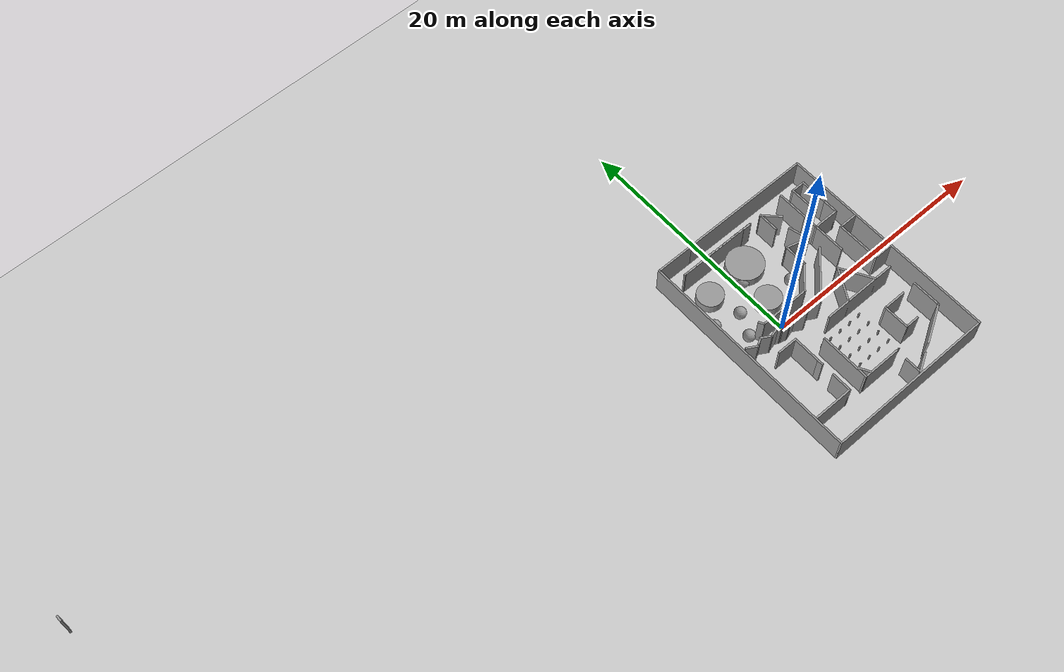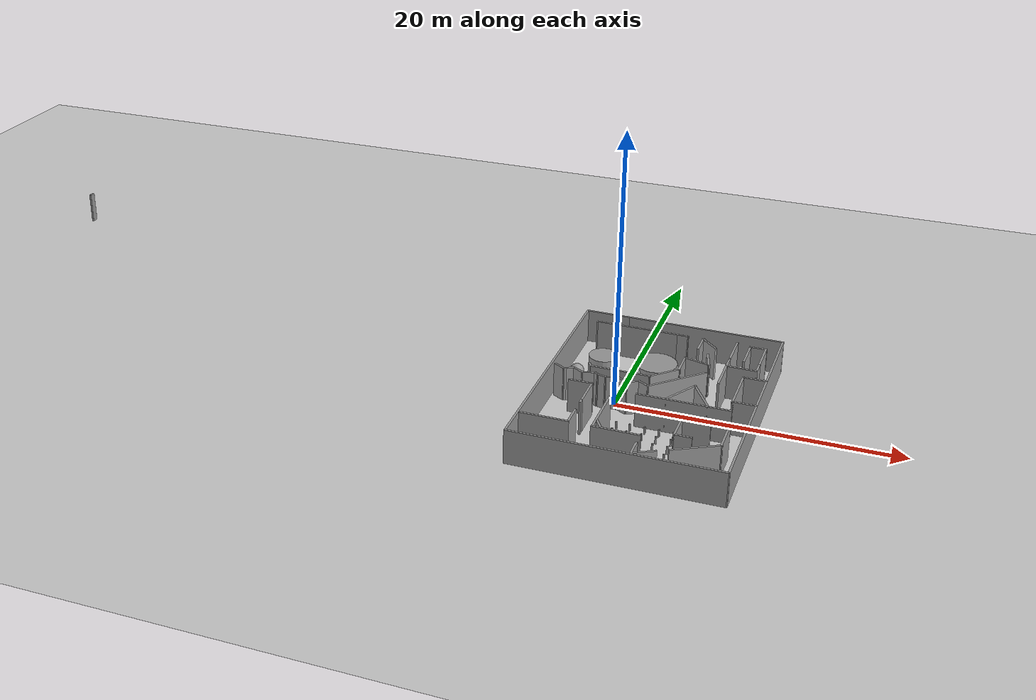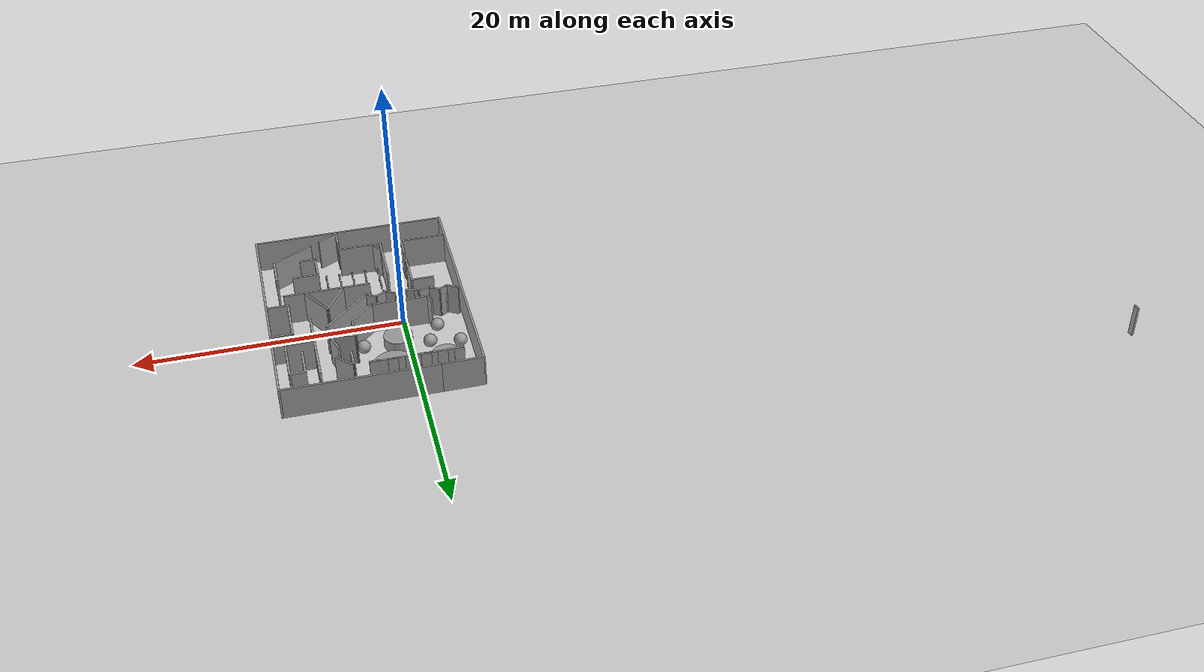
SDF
<sdf version="1.7">
 <world name="default">
  <scene><ambient>0.4 0.4 0.4 1</ambient><background>0.7 0.7 0.7 1</background><shadows>1</shadows></scene>
  <light name="sun" type="directional">
   <pose>0 0 10 0 -0 0</pose>
   <diffuse>0.8 0.8 0.8 1</diffuse>
   <specular>0.2 0.2 0.2 1</specular>
   <attenuation>
    <range>1000</range>
    <constant>0.9</constant>
    <linear>0.01</linear>
    <quadratic>0.001</quadratic>
   </attenuation>
   <direction>-0.5 0.1 -0.9</direction>
   <spot><inner_angle>0</inner_angle><outer_angle>0</outer_angle><falloff>0</falloff></spot>
  </light>
  <model name="ground_plane">
   <static>1</static>
   <link name="link">
    <collision name="collision">
     <geometry><plane><normal>0 0 1</normal><size>100 100</size></plane></geometry>
     <surface><friction><ode><mu>100</mu><mu2>50</mu2></ode></friction></surface>
    </collision>
    <visual name="visual">
     <cast_shadows>0</cast_shadows>
     <geometry><plane><normal>0 0 1</normal><size>100 100</size></plane></geometry>
     <material>
      <script><uri>file://media/materials/scripts/gazebo.material</uri><name>Gazebo/Grey</name></script>
     </material>
    </visual>
   </link>
  </model>
  <physics type="ode">
   <real_time_update_rate>0</real_time_update_rate>
   <max_step_size>0.001</max_step_size>
   <real_time_factor>1</real_time_factor>
   <ode>
    <solver>
     <type>quick</type>
     <iters>150</iters>
     <precon_iters>0</precon_iters>
     <sor>1.4</sor>
     <use_dynamic_moi_rescaling>1</use_dynamic_moi_rescaling>
    </solver>
    <constraints>
     <cfm>1e-05</cfm>
     <erp>0.2</erp>
     <contact_max_correcting_vel>2000</contact_max_correcting_vel>
     <contact_surface_layer>0.01</contact_surface_layer>
    </constraints>
   </ode>
  </physics>
  <gravity>0 0 -9.8</gravity>
  <magnetic_field>6e-06 2.3e-05 -4.2e-05</magnetic_field>
  <atmosphere type="adiabatic"/>
  <spherical_coordinates>
   <surface_model>EARTH_WGS84</surface_model>
   <latitude_deg>0</latitude_deg>
   <longitude_deg>0</longitude_deg>
   <elevation>0</elevation>
   <heading_deg>0</heading_deg>
  </spherical_coordinates>
  <model name="Base_square">
   <pose>-21.2675 2.85477 0 0 -0 0</pose>
   <link name="Wall_17">
    <collision name="Wall_17_Collision">
     <geometry><box><size>18.75 0.15 2.5</size></box></geometry>
     <pose>0 0 1.25 0 -0 0</pose>
    </collision>
    <visual name="Wall_17_Visual">
     <pose>0 0 1.25 0 -0 0</pose>
     <geometry><box><size>18.75 0.15 2.5</size></box></geometry>
     <material>
      <script><uri>file://media/materials/scripts/gazebo.material</uri><name>Gazebo/Grey</name></script>
      <ambient>1 1 1 1</ambient>
     </material>
     <meta><layer>0</layer></meta>
    </visual>
    <pose>16.7268 -3.44544 0 0 -0 -1.5708</pose>
   </link>
   <link name="Wall_18">
    <collision name="Wall_18_Collision">
     <geometry><box><size>14.6395 0.15 2.5</size></box></geometry>
     <pose>0 0 1.25 0 -0 0</pose>
    </collision>
    <visual name="Wall_18_Visual">
     <pose>0 0 1.25 0 -0 0</pose>
     <geometry><box><size>14.6395 0.15 2.5</size></box></geometry>
     <material>
      <script><uri>file://media/materials/scripts/gazebo.material</uri><name>Gazebo/Grey</name></script>
      <ambient>1 1 1 1</ambient>
     </material>
     <meta><layer>0</layer></meta>
    </visual>
    <pose>23.9714 -12.7722 0 0 -0 0.003693</pose>
   </link>
   <link name="Wall_19">
    <collision name="Wall_19_Collision">
     <geometry><box><size>18.75 0.15 2.5</size></box></geometry>
     <pose>0 0 1.25 0 -0 0</pose>
    </collision>
    <visual name="Wall_19_Visual">
     <pose>0 0 1.25 0 -0 0</pose>
     <geometry><box><size>18.75 0.15 2.5</size></box></geometry>
     <material>
      <script><uri>file://media/materials/scripts/gazebo.material</uri><name>Gazebo/Grey</name></script>
      <ambient>1 1 1 1</ambient>
     </material>
     <meta><layer>0</layer></meta>
    </visual>
    <pose>31.216 -3.44544 0 0 -0 1.5708</pose>
   </link>
   <link name="Wall_20">
    <collision name="Wall_20_Collision">
     <geometry><box><size>11.5 0.15 2.5</size></box></geometry>
     <pose>0 0 1.25 0 -0 0</pose>
    </collision>
    <visual name="Wall_20_Visual">
     <pose>0 0 1.25 0 -0 0</pose>
     <geometry><box><size>11.5 0.15 2.5</size></box></geometry>
     <material>
      <script><uri>file://media/materials/scripts/gazebo.material</uri><name>Gazebo/Grey</name></script>
      <ambient>1 1 1 1</ambient>
     </material>
     <meta><layer>0</layer></meta>
    </visual>
    <pose>25.541 5.85456 0 0 -0 3.14159</pose>
   </link>
   <link name="Wall_32">
    <collision name="Wall_32_Collision">
     <geometry><box><size>3.25 0.15 2.5</size></box></geometry>
     <pose>0 0 1.25 0 -0 0</pose>
    </collision>
    <visual name="Wall_32_Visual">
     <pose>0 0 1.25 0 -0 0</pose>
     <geometry><box><size>3.25 0.15 2.5</size></box></geometry>
     <material>
      <script><uri>file://media/materials/scripts/gazebo.material</uri><name>Gazebo/Grey</name></script>
      <ambient>1 1 1 1</ambient>
     </material>
     <meta><layer>0</layer></meta>
    </visual>
    <pose>18.316 5.85456 0 0 -0 3.14159</pose>
   </link>
   <link name="Wall_8">
    <collision name="Wall_8_Collision">
     <geometry><box><size>0.5 0.15 2.5</size></box></geometry>
     <pose>0 0 1.25 0 -0 0</pose>
    </collision>
    <visual name="Wall_8_Visual">
     <pose>0 0 1.25 0 -0 0</pose>
     <geometry><box><size>0.5 0.15 2.5</size></box></geometry>
     <material>
      <script><uri>file://media/materials/scripts/gazebo.material</uri><name>Gazebo/Grey</name></script>
      <ambient>1 1 1 1</ambient>
     </material>
     <meta><layer>0</layer></meta>
    </visual>
    <pose>-31.2164 12.6242 0 0 -0 -1.5708</pose>
   </link>
   <static>1</static>
  </model>
  <model name="complicated_walls">
   <pose>2.75281 -1.1927 0 0 -0 0</pose>
   <link name="Wall_101">
    <collision name="Wall_101_Collision">
     <geometry><box><size>2.25 0.15 2.5</size></box></geometry>
     <pose>0 0 1.25 0 -0 0</pose>
    </collision>
    <visual name="Wall_101_Visual">
     <pose>0 0 1.25 0 -0 0</pose>
     <geometry><box><size>2.25 0.15 2.5</size></box></geometry>
     <material>
      <script><uri>file://media/materials/scripts/gazebo.material</uri><name>Gazebo/Grey</name></script>
      <ambient>1 1 1 1</ambient>
     </material>
     <meta><layer>0</layer></meta>
    </visual>
    <pose>5.22484 4.90268 0 0 -0 0</pose>
   </link>
   <link name="Wall_102">
    <collision name="Wall_102_Collision">
     <geometry><box><size>1.25 0.15 2.5</size></box></geometry>
     <pose>0 0 1.25 0 -0 0</pose>
    </collision>
    <visual name="Wall_102_Visual">
     <pose>0 0 1.25 0 -0 0</pose>
     <geometry><box><size>1.25 0.15 2.5</size></box></geometry>
     <material>
      <script><uri>file://media/materials/scripts/gazebo.material</uri><name>Gazebo/Grey</name></script>
      <ambient>1 1 1 1</ambient>
     </material>
     <meta><layer>0</layer></meta>
    </visual>
    <pose>6.27484 5.45268 0 0 -0 1.5708</pose>
   </link>
   <link name="Wall_108">
    <collision name="Wall_108_Collision">
     <geometry><box><size>2.5 0.15 2.5</size></box></geometry>
     <pose>0 0 1.25 0 -0 0</pose>
    </collision>
    <visual name="Wall_108_Visual">
     <pose>0 0 1.25 0 -0 0</pose>
     <geometry><box><size>2.5 0.15 2.5</size></box></geometry>
     <material>
      <script><uri>file://media/materials/scripts/gazebo.material</uri><name>Gazebo/Grey</name></script>
      <ambient>1 1 1 1</ambient>
     </material>
     <meta><layer>0</layer></meta>
    </visual>
    <pose>6.27484 7.17768 0 0 -0 1.5708</pose>
   </link>
   <link name="Wall_109">
    <collision name="Wall_109_Collision">
     <geometry><box><size>1.25 0.15 2.5</size></box></geometry>
     <pose>0 0 1.25 0 -0 0</pose>
    </collision>
    <visual name="Wall_109_Visual">
     <pose>0 0 1.25 0 -0 0</pose>
     <geometry><box><size>1.25 0.15 2.5</size></box></geometry>
     <material>
      <script><uri>file://media/materials/scripts/gazebo.material</uri><name>Gazebo/Grey</name></script>
      <ambient>1 1 1 1</ambient>
     </material>
     <meta><layer>0</layer></meta>
    </visual>
    <pose>5.72484 8.35268 0 0 -0 3.14159</pose>
   </link>
   <link name="Wall_110">
    <collision name="Wall_110_Collision">
     <geometry><box><size>2.5 0.15 2.5</size></box></geometry>
     <pose>0 0 1.25 0 -0 0</pose>
    </collision>
    <visual name="Wall_110_Visual">
     <pose>0 0 1.25 0 -0 0</pose>
     <geometry><box><size>2.5 0.15 2.5</size></box></geometry>
     <material>
      <script><uri>file://media/materials/scripts/gazebo.material</uri><name>Gazebo/Grey</name></script>
      <ambient>1 1 1 1</ambient>
     </material>
     <meta><layer>0</layer></meta>
    </visual>
    <pose>5.17484 7.17768 0 0 -0 -1.5708</pose>
   </link>
   <link name="Wall_112">
    <collision name="Wall_112_Collision">
     <geometry><box><size>1.75 0.15 2.5</size></box></geometry>
     <pose>0 0 1.25 0 -0 0</pose>
    </collision>
    <visual name="Wall_112_Visual">
     <pose>0 0 1.25 0 -0 0</pose>
     <geometry><box><size>1.75 0.15 2.5</size></box></geometry>
     <material>
      <script><uri>file://media/materials/scripts/gazebo.material</uri><name>Gazebo/Grey</name></script>
      <ambient>1 1 1 1</ambient>
     </material>
     <meta><layer>0</layer></meta>
    </visual>
    <pose>2.32734 7.82443 0 0 -0 2.35619</pose>
   </link>
   <link name="Wall_113">
    <collision name="Wall_113_Collision">
     <geometry><box><size>1.75 0.15 2.5</size></box></geometry>
     <pose>0 0 1.25 0 -0 0</pose>
    </collision>
    <visual name="Wall_113_Visual">
     <pose>0 0 1.25 0 -0 0</pose>
     <geometry><box><size>1.75 0.15 2.5</size></box></geometry>
     <material>
      <script><uri>file://media/materials/scripts/gazebo.material</uri><name>Gazebo/Grey</name></script>
      <ambient>1 1 1 1</ambient>
     </material>
     <meta><layer>0</layer></meta>
    </visual>
    <pose>1.76165 7.59012 0 0 -0 -1.5708</pose>
   </link>
   <link name="Wall_115">
    <collision name="Wall_115_Collision">
     <geometry><box><size>1.75 0.15 2.5</size></box></geometry>
     <pose>0 0 1.25 0 -0 0</pose>
    </collision>
    <visual name="Wall_115_Visual">
     <pose>0 0 1.25 0 -0 0</pose>
     <geometry><box><size>1.75 0.15 2.5</size></box></geometry>
     <material>
      <script><uri>file://media/materials/scripts/gazebo.material</uri><name>Gazebo/Grey</name></script>
      <ambient>1 1 1 1</ambient>
     </material>
     <meta><layer>0</layer></meta>
    </visual>
    <pose>2.79418 5.38476 0 0 -0 -1.309</pose>
   </link>
   <link name="Wall_116">
    <collision name="Wall_116_Collision">
     <geometry><box><size>2 0.15 2.5</size></box></geometry>
     <pose>0 0 1.25 0 -0 0</pose>
    </collision>
    <visual name="Wall_116_Visual">
     <pose>0 0 1.25 0 -0 0</pose>
     <geometry><box><size>2 0.15 2.5</size></box></geometry>
     <material>
      <script><uri>file://media/materials/scripts/gazebo.material</uri><name>Gazebo/Grey</name></script>
      <ambient>1 1 1 1</ambient>
     </material>
     <meta><layer>0</layer></meta>
    </visual>
    <pose>2.10775 4.85142 0 0 -0 2.87979</pose>
   </link>
   <link name="Wall_118">
    <collision name="Wall_118_Collision">
     <geometry><box><size>2 0.15 2.5</size></box></geometry>
     <pose>0 0 1.25 0 -0 0</pose>
    </collision>
    <visual name="Wall_118_Visual">
     <pose>0 0 1.25 0 -0 0</pose>
     <geometry><box><size>2 0.15 2.5</size></box></geometry>
     <material>
      <script><uri>file://media/materials/scripts/gazebo.material</uri><name>Gazebo/Grey</name></script>
      <ambient>1 1 1 1</ambient>
     </material>
     <meta><layer>0</layer></meta>
    </visual>
    <pose>1.21427 4.16583 0 0 -0 -1.5708</pose>
   </link>
   <link name="Wall_121">
    <collision name="Wall_121_Collision">
     <geometry><box><size>2.5 0.15 2.5</size></box></geometry>
     <pose>0 0 1.25 0 -0 0</pose>
    </collision>
    <visual name="Wall_121_Visual">
     <pose>0 0 1.25 0 -0 0</pose>
     <geometry><box><size>2.5 0.15 2.5</size></box></geometry>
     <material>
      <script><uri>file://media/materials/scripts/gazebo.material</uri><name>Gazebo/Grey</name></script>
      <ambient>1 1 1 1</ambient>
     </material>
     <meta><layer>0</layer></meta>
    </visual>
    <pose>0.38342 2.40998 0 0 -0 -2.35619</pose>
   </link>
   <link name="Wall_122">
    <collision name="Wall_122_Collision">
     <geometry><box><size>4.25 0.15 2.5</size></box></geometry>
     <pose>0 0 1.25 0 -0 0</pose>
    </collision>
    <visual name="Wall_122_Visual">
     <pose>0 0 1.25 0 -0 0</pose>
     <geometry><box><size>4.25 0.15 2.5</size></box></geometry>
     <material>
      <script><uri>file://media/materials/scripts/gazebo.material</uri><name>Gazebo/Grey</name></script>
      <ambient>1 1 1 1</ambient>
     </material>
     <meta><layer>0</layer></meta>
    </visual>
    <pose>-2.49743 1.57913 0 0 -0 3.14159</pose>
   </link>
   <link name="Wall_126">
    <collision name="Wall_126_Collision">
     <geometry><box><size>0.75 0.15 2.5</size></box></geometry>
     <pose>0 0 1.25 0 -0 0</pose>
    </collision>
    <visual name="Wall_126_Visual">
     <pose>0 0 1.25 0 -0 0</pose>
     <geometry><box><size>0.75 0.15 2.5</size></box></geometry>
     <material>
      <script><uri>file://media/materials/scripts/gazebo.material</uri><name>Gazebo/Grey</name></script>
      <ambient>1 1 1 1</ambient>
     </material>
     <meta><layer>0</layer></meta>
    </visual>
    <pose>0.251573 8.36592 0 0 -0 0</pose>
   </link>
   <link name="Wall_128">
    <collision name="Wall_128_Collision">
     <geometry><box><size>0.75 0.15 2.5</size></box></geometry>
     <pose>0 0 1.25 0 -0 0</pose>
    </collision>
    <visual name="Wall_128_Visual">
     <pose>0 0 1.25 0 -0 0</pose>
     <geometry><box><size>0.75 0.15 2.5</size></box></geometry>
     <material>
      <script><uri>file://media/materials/scripts/gazebo.material</uri><name>Gazebo/Grey</name></script>
      <ambient>1 1 1 1</ambient>
     </material>
     <meta><layer>0</layer></meta>
    </visual>
    <pose>-0.995716 8.40637 0 0 -0 3.14159</pose>
   </link>
   <link name="Wall_130">
    <collision name="Wall_130_Collision">
     <geometry><box><size>0.75 0.15 2.5</size></box></geometry>
     <pose>0 0 1.25 0 -0 0</pose>
    </collision>
    <visual name="Wall_130_Visual">
     <pose>0 0 1.25 0 -0 0</pose>
     <geometry><box><size>0.75 0.15 2.5</size></box></geometry>
     <material>
      <script><uri>file://media/materials/scripts/gazebo.material</uri><name>Gazebo/Grey</name></script>
      <ambient>1 1 1 1</ambient>
     </material>
     <meta><layer>0</layer></meta>
    </visual>
    <pose>-2.24241 8.39485 0 0 -0 3.14159</pose>
   </link>
   <link name="Wall_132">
    <collision name="Wall_132_Collision">
     <geometry><box><size>0.75 0.15 2.5</size></box></geometry>
     <pose>0 0 1.25 0 -0 0</pose>
    </collision>
    <visual name="Wall_132_Visual">
     <pose>0 0 1.25 0 -0 0</pose>
     <geometry><box><size>0.75 0.15 2.5</size></box></geometry>
     <material>
      <script><uri>file://media/materials/scripts/gazebo.material</uri><name>Gazebo/Grey</name></script>
      <ambient>1 1 1 1</ambient>
     </material>
     <meta><layer>0</layer></meta>
    </visual>
    <pose>-3.37562 8.42145 0 0 -0 3.14159</pose>
   </link>
   <link name="Wall_134">
    <collision name="Wall_134_Collision">
     <geometry><box><size>0.75 0.15 2.5</size></box></geometry>
     <pose>0 0 1.25 0 -0 0</pose>
    </collision>
    <visual name="Wall_134_Visual">
     <pose>0 0 1.25 0 -0 0</pose>
     <geometry><box><size>0.75 0.15 2.5</size></box></geometry>
     <material>
      <script><uri>file://media/materials/scripts/gazebo.material</uri><name>Gazebo/Grey</name></script>
      <ambient>1 1 1 1</ambient>
     </material>
     <meta><layer>0</layer></meta>
    </visual>
    <pose>-4.57263 8.39485 0 0 -0 3.14159</pose>
   </link>
   <link name="Wall_136">
    <collision name="Wall_136_Collision">
     <geometry><box><size>0.75 0.15 2.5</size></box></geometry>
     <pose>0 0 1.25 0 -0 0</pose>
    </collision>
    <visual name="Wall_136_Visual">
     <pose>0 0 1.25 0 -0 0</pose>
     <geometry><box><size>0.75 0.15 2.5</size></box></geometry>
     <material>
      <script><uri>file://media/materials/scripts/gazebo.material</uri><name>Gazebo/Grey</name></script>
      <ambient>1 1 1 1</ambient>
     </material>
     <meta><layer>0</layer></meta>
    </visual>
    <pose>-5.78024 8.39485 0 0 -0 3.14159</pose>
   </link>
   <link name="Wall_35">
    <collision name="Wall_35_Collision">
     <geometry><box><size>3.5 0.15 2.5</size></box></geometry>
     <pose>0 0 1.25 0 -0 0</pose>
    </collision>
    <visual name="Wall_35_Visual">
     <pose>0 0 1.25 0 -0 0</pose>
     <geometry><box><size>3.5 0.15 2.5</size></box></geometry>
     <material>
      <script><uri>file://media/materials/scripts/gazebo.material</uri><name>Gazebo/Grey</name></script>
      <ambient>1 1 1 1</ambient>
     </material>
     <meta><layer>0</layer></meta>
    </visual>
    <pose>-5.51959 -6.24325 0 0 -0 3.14159</pose>
   </link>
   <link name="Wall_37">
    <collision name="Wall_37_Collision">
     <geometry><box><size>1.75 0.15 2.5</size></box></geometry>
     <pose>0 0 1.25 0 -0 0</pose>
    </collision>
    <visual name="Wall_37_Visual">
     <pose>0 0 1.25 0 -0 0</pose>
     <geometry><box><size>1.75 0.15 2.5</size></box></geometry>
     <material>
      <script><uri>file://media/materials/scripts/gazebo.material</uri><name>Gazebo/Grey</name></script>
      <ambient>1 1 1 1</ambient>
     </material>
     <meta><layer>0</layer></meta>
    </visual>
    <pose>-3.84459 -5.44325 0 0 -0 1.5708</pose>
   </link>
   <link name="Wall_40">
    <collision name="Wall_40_Collision">
     <geometry><box><size>0.5 0.15 2.5</size></box></geometry>
     <pose>0 0 1.25 0 -0 0</pose>
    </collision>
    <visual name="Wall_40_Visual">
     <pose>0 0 1.25 0 -0 0</pose>
     <geometry><box><size>0.5 0.15 2.5</size></box></geometry>
     <material>
      <script><uri>file://media/materials/scripts/gazebo.material</uri><name>Gazebo/Grey</name></script>
      <ambient>1 1 1 1</ambient>
     </material>
     <meta><layer>0</layer></meta>
    </visual>
    <pose>-3.83383 -3.33511 0 0 -0 1.5708</pose>
   </link>
   <link name="Wall_42">
    <collision name="Wall_42_Collision">
     <geometry><box><size>2.5 0.15 2.5</size></box></geometry>
     <pose>0 0 1.25 0 -0 0</pose>
    </collision>
    <visual name="Wall_42_Visual">
     <pose>0 0 1.25 0 -0 0</pose>
     <geometry><box><size>2.5 0.15 2.5</size></box></geometry>
     <material>
      <script><uri>file://media/materials/scripts/gazebo.material</uri><name>Gazebo/Grey</name></script>
      <ambient>1 1 1 1</ambient>
     </material>
     <meta><layer>0</layer></meta>
    </visual>
    <pose>-3.83383 -1.98511 0 0 -0 1.5708</pose>
   </link>
   <link name="Wall_45">
    <collision name="Wall_45_Collision">
     <geometry><box><size>4.25 0.15 2.5</size></box></geometry>
     <pose>0 0 1.25 0 -0 0</pose>
    </collision>
    <visual name="Wall_45_Visual">
     <pose>0 0 1.25 0 -0 0</pose>
     <geometry><box><size>4.25 0.15 2.5</size></box></geometry>
     <material>
      <script><uri>file://media/materials/scripts/gazebo.material</uri><name>Gazebo/Grey</name></script>
      <ambient>1 1 1 1</ambient>
     </material>
     <meta><layer>0</layer></meta>
    </visual>
    <pose>-2.20117 -4.24331 0 0 -0 -1.5708</pose>
   </link>
   <link name="Wall_46">
    <collision name="Wall_46_Collision">
     <geometry><box><size>3.34054 0.15 2.5</size></box></geometry>
     <pose>0 0 1.25 0 -0 0</pose>
    </collision>
    <visual name="Wall_46_Visual">
     <pose>0 0 1.25 0 -0 0</pose>
     <geometry><box><size>3.34054 0.15 2.5</size></box></geometry>
     <material>
      <script><uri>file://media/materials/scripts/gazebo.material</uri><name>Gazebo/Grey</name></script>
      <ambient>1 1 1 1</ambient>
     </material>
     <meta><layer>0</layer></meta>
    </visual>
    <pose>-0.641081 -6.29331 0 0 -0 0</pose>
   </link>
   <link name="Wall_49">
    <collision name="Wall_49_Collision">
     <geometry><box><size>1.5 0.15 2.5</size></box></geometry>
     <pose>0 0 1.25 0 -0 0</pose>
    </collision>
    <visual name="Wall_49_Visual">
     <pose>0 0 1.25 0 -0 0</pose>
     <geometry><box><size>1.5 0.15 2.5</size></box></geometry>
     <material>
      <script><uri>file://media/materials/scripts/gazebo.material</uri><name>Gazebo/Grey</name></script>
      <ambient>1 1 1 1</ambient>
     </material>
     <meta><layer>0</layer></meta>
    </visual>
    <pose>0.983895 -7.92143 0 0 -0 -1.5708</pose>
   </link>
   <link name="Wall_53">
    <collision name="Wall_53_Collision">
     <geometry><box><size>1.75 0.15 2.5</size></box></geometry>
     <pose>0 0 1.25 0 -0 0</pose>
    </collision>
    <visual name="Wall_53_Visual">
     <pose>0 0 1.25 0 -0 0</pose>
     <geometry><box><size>1.75 0.15 2.5</size></box></geometry>
     <material>
      <script><uri>file://media/materials/scripts/gazebo.material</uri><name>Gazebo/Grey</name></script>
      <ambient>1 1 1 1</ambient>
     </material>
     <meta><layer>0</layer></meta>
    </visual>
    <pose>1.67671 -8.19642 0 0 -0 0.523599</pose>
   </link>
   <link name="Wall_55">
    <collision name="Wall_55_Collision">
     <geometry><box><size>3.5 0.15 2.5</size></box></geometry>
     <pose>0 0 1.25 0 -0 0</pose>
    </collision>
    <visual name="Wall_55_Visual">
     <pose>0 0 1.25 0 -0 0</pose>
     <geometry><box><size>3.5 0.15 2.5</size></box></geometry>
     <material>
      <script><uri>file://media/materials/scripts/gazebo.material</uri><name>Gazebo/Grey</name></script>
      <ambient>1 1 1 1</ambient>
     </material>
     <meta><layer>0</layer></meta>
    </visual>
    <pose>4.62687 -6.52097 0 0 -0 0.523599</pose>
   </link>
   <link name="Wall_57">
    <collision name="Wall_57_Collision">
     <geometry><box><size>2.5 0.15 2.5</size></box></geometry>
     <pose>0 0 1.25 0 -0 0</pose>
    </collision>
    <visual name="Wall_57_Visual">
     <pose>0 0 1.25 0 -0 0</pose>
     <geometry><box><size>2.5 0.15 2.5</size></box></geometry>
     <material>
      <script><uri>file://media/materials/scripts/gazebo.material</uri><name>Gazebo/Grey</name></script>
      <ambient>1 1 1 1</ambient>
     </material>
     <meta><layer>0</layer></meta>
    </visual>
    <pose>6.07746 -4.50847 0 0 -0 1.5708</pose>
   </link>
   <link name="Wall_59">
    <collision name="Wall_59_Collision">
     <geometry><box><size>2.25 0.15 2.5</size></box></geometry>
     <pose>0 0 1.25 0 -0 0</pose>
    </collision>
    <visual name="Wall_59_Visual">
     <pose>0 0 1.25 0 -0 0</pose>
     <geometry><box><size>2.25 0.15 2.5</size></box></geometry>
     <material>
      <script><uri>file://media/materials/scripts/gazebo.material</uri><name>Gazebo/Grey</name></script>
      <ambient>1 1 1 1</ambient>
     </material>
     <meta><layer>0</layer></meta>
    </visual>
    <pose>2.97746 -4.38347 0 0 -0 -1.5708</pose>
   </link>
   <link name="Wall_60">
    <collision name="Wall_60_Collision">
     <geometry><box><size>1.25 0.15 2.5</size></box></geometry>
     <pose>0 0 1.25 0 -0 0</pose>
    </collision>
    <visual name="Wall_60_Visual">
     <pose>0 0 1.25 0 -0 0</pose>
     <geometry><box><size>1.25 0.15 2.5</size></box></geometry>
     <material>
      <script><uri>file://media/materials/scripts/gazebo.material</uri><name>Gazebo/Grey</name></script>
      <ambient>1 1 1 1</ambient>
     </material>
     <meta><layer>0</layer></meta>
    </visual>
    <pose>3.52746 -5.43347 0 0 -0 0</pose>
   </link>
   <link name="Wall_62">
    <collision name="Wall_62_Collision">
     <geometry><box><size>2 0.15 2.5</size></box></geometry>
     <pose>0 0 1.25 0 -0 0</pose>
    </collision>
    <visual name="Wall_62_Visual">
     <pose>0 0 1.25 0 -0 0</pose>
     <geometry><box><size>2 0.15 2.5</size></box></geometry>
     <material>
      <script><uri>file://media/materials/scripts/gazebo.material</uri><name>Gazebo/Grey</name></script>
      <ambient>1 1 1 1</ambient>
     </material>
     <meta><layer>0</layer></meta>
    </visual>
    <pose>3.90246 -3.33347 0 0 -0 0</pose>
   </link>
   <link name="Wall_64">
    <collision name="Wall_64_Collision">
     <geometry><box><size>1 0.15 2.5</size></box></geometry>
     <pose>0 0 1.25 0 -0 0</pose>
    </collision>
    <visual name="Wall_64_Visual">
     <pose>0 0 1.25 0 -0 0</pose>
     <geometry><box><size>1 0.15 2.5</size></box></geometry>
     <material>
      <script><uri>file://media/materials/scripts/gazebo.material</uri><name>Gazebo/Grey</name></script>
      <ambient>1 1 1 1</ambient>
     </material>
     <meta><layer>0</layer></meta>
    </visual>
    <pose>-1.90109 -5.83585 0 0 -0 -1.0472</pose>
   </link>
   <link name="Wall_66">
    <collision name="Wall_66_Collision">
     <geometry><box><size>6.5 0.15 2.5</size></box></geometry>
     <pose>0 0 1.25 0 -0 0</pose>
    </collision>
    <visual name="Wall_66_Visual">
     <pose>0 0 1.25 0 -0 0</pose>
     <geometry><box><size>6.5 0.15 2.5</size></box></geometry>
     <material>
      <script><uri>file://media/materials/scripts/gazebo.material</uri><name>Gazebo/Grey</name></script>
      <ambient>1 1 1 1</ambient>
     </material>
     <meta><layer>0</layer></meta>
    </visual>
    <pose>2.56547 -1.15181 0 0 -0 0</pose>
   </link>
   <link name="Wall_68">
    <collision name="Wall_68_Collision">
     <geometry><box><size>3 0.15 2.5</size></box></geometry>
     <pose>0 0 1.25 0 -0 0</pose>
    </collision>
    <visual name="Wall_68_Visual">
     <pose>0 0 1.25 0 -0 0</pose>
     <geometry><box><size>3 0.15 2.5</size></box></geometry>
     <material>
      <script><uri>file://media/materials/scripts/gazebo.material</uri><name>Gazebo/Grey</name></script>
      <ambient>1 1 1 1</ambient>
     </material>
     <meta><layer>0</layer></meta>
    </visual>
    <pose>2.06907 0.105403 0 0 -0 1.0472</pose>
   </link>
   <link name="Wall_69">
    <collision name="Wall_69_Collision">
     <geometry><box><size>3 0.15 2.5</size></box></geometry>
     <pose>0 0 1.25 0 -0 0</pose>
    </collision>
    <visual name="Wall_69_Visual">
     <pose>0 0 1.25 0 -0 0</pose>
     <geometry><box><size>3 0.15 2.5</size></box></geometry>
     <material>
      <script><uri>file://media/materials/scripts/gazebo.material</uri><name>Gazebo/Grey</name></script>
      <ambient>1 1 1 1</ambient>
     </material>
     <meta><layer>0</layer></meta>
    </visual>
    <pose>3.49407 0.105403 0 0 -0 -1.0472</pose>
   </link>
   <link name="Wall_71">
    <collision name="Wall_71_Collision">
     <geometry><box><size>1.75 0.15 2.5</size></box></geometry>
     <pose>0 0 1.25 0 -0 0</pose>
    </collision>
    <visual name="Wall_71_Visual">
     <pose>0 0 1.25 0 -0 0</pose>
     <geometry><box><size>1.75 0.15 2.5</size></box></geometry>
     <material>
      <script><uri>file://media/materials/scripts/gazebo.material</uri><name>Gazebo/Grey</name></script>
      <ambient>1 1 1 1</ambient>
     </material>
     <meta><layer>0</layer></meta>
    </visual>
    <pose>-4.63383 -0.810111 0 0 -0 3.14159</pose>
   </link>
   <link name="Wall_73">
    <collision name="Wall_73_Collision">
     <geometry><box><size>0.75 0.15 2.5</size></box></geometry>
     <pose>0 0 1.25 0 -0 0</pose>
    </collision>
    <visual name="Wall_73_Visual">
     <pose>0 0 1.25 0 -0 0</pose>
     <geometry><box><size>0.75 0.15 2.5</size></box></geometry>
     <material>
      <script><uri>file://media/materials/scripts/gazebo.material</uri><name>Gazebo/Grey</name></script>
      <ambient>1 1 1 1</ambient>
     </material>
     <meta><layer>0</layer></meta>
    </visual>
    <pose>-3.51347 0.476492 0 0 -0 -0.261799</pose>
   </link>
   <link name="Wall_74">
    <collision name="Wall_74_Collision">
     <geometry><box><size>1 0.15 2.5</size></box></geometry>
     <pose>0 0 1.25 0 -0 0</pose>
    </collision>
    <visual name="Wall_74_Visual">
     <pose>0 0 1.25 0 -0 0</pose>
     <geometry><box><size>1 0.15 2.5</size></box></geometry>
     <material>
      <script><uri>file://media/materials/scripts/gazebo.material</uri><name>Gazebo/Grey</name></script>
      <ambient>1 1 1 1</ambient>
     </material>
     <meta><layer>0</layer></meta>
    </visual>
    <pose>-2.81317 0.508845 0 0 -0 0.261799</pose>
   </link>
   <link name="Wall_75">
    <collision name="Wall_75_Collision">
     <geometry><box><size>1 0.15 2.5</size></box></geometry>
     <pose>0 0 1.25 0 -0 0</pose>
    </collision>
    <visual name="Wall_75_Visual">
     <pose>0 0 1.25 0 -0 0</pose>
     <geometry><box><size>1 0.15 2.5</size></box></geometry>
     <material>
      <script><uri>file://media/materials/scripts/gazebo.material</uri><name>Gazebo/Grey</name></script>
      <ambient>1 1 1 1</ambient>
     </material>
     <meta><layer>0</layer></meta>
    </visual>
    <pose>-2.03459 0.406343 0 0 -0 -0.523599</pose>
   </link>
   <link name="Wall_76">
    <collision name="Wall_76_Collision">
     <geometry><box><size>1 0.15 2.5</size></box></geometry>
     <pose>0 0 1.25 0 -0 0</pose>
    </collision>
    <visual name="Wall_76_Visual">
     <pose>0 0 1.25 0 -0 0</pose>
     <geometry><box><size>1 0.15 2.5</size></box></geometry>
     <material>
      <script><uri>file://media/materials/scripts/gazebo.material</uri><name>Gazebo/Grey</name></script>
      <ambient>1 1 1 1</ambient>
     </material>
     <meta><layer>0</layer></meta>
    </visual>
    <pose>-1.29847 0.406343 0 0 -0 0.523599</pose>
   </link>
   <link name="Wall_78">
    <collision name="Wall_78_Collision">
     <geometry><box><size>0.5 0.15 2.5</size></box></geometry>
     <pose>0 0 1.25 0 -0 0</pose>
    </collision>
    <visual name="Wall_78_Visual">
     <pose>0 0 1.25 0 -0 0</pose>
     <geometry><box><size>0.5 0.15 2.5</size></box></geometry>
     <material>
      <script><uri>file://media/materials/scripts/gazebo.material</uri><name>Gazebo/Grey</name></script>
      <ambient>1 1 1 1</ambient>
     </material>
     <meta><layer>0</layer></meta>
    </visual>
    <pose>-3.9548 0.641638 0 0 -0 2.61799</pose>
   </link>
   <link name="Wall_79">
    <collision name="Wall_79_Collision">
     <geometry><box><size>1 0.15 2.5</size></box></geometry>
     <pose>0 0 1.25 0 -0 0</pose>
    </collision>
    <visual name="Wall_79_Visual">
     <pose>0 0 1.25 0 -0 0</pose>
     <geometry><box><size>1 0.15 2.5</size></box></geometry>
     <material>
      <script><uri>file://media/materials/scripts/gazebo.material</uri><name>Gazebo/Grey</name></script>
      <ambient>1 1 1 1</ambient>
     </material>
     <meta><layer>0</layer></meta>
    </visual>
    <pose>-4.51687 0.61914 0 0 -0 -2.87979</pose>
   </link>
   <link name="Wall_80">
    <collision name="Wall_80_Collision">
     <geometry><box><size>1 0.15 2.5</size></box></geometry>
     <pose>0 0 1.25 0 -0 0</pose>
    </collision>
    <visual name="Wall_80_Visual">
     <pose>0 0 1.25 0 -0 0</pose>
     <geometry><box><size>1 0.15 2.5</size></box></geometry>
     <material>
      <script><uri>file://media/materials/scripts/gazebo.material</uri><name>Gazebo/Grey</name></script>
      <ambient>1 1 1 1</ambient>
     </material>
     <meta><layer>0</layer></meta>
    </visual>
    <pose>-5.29545 0.721642 0 0 -0 2.61799</pose>
   </link>
   <link name="Wall_81">
    <collision name="Wall_81_Collision">
     <geometry><box><size>0.75 0.15 2.5</size></box></geometry>
     <pose>0 0 1.25 0 -0 0</pose>
    </collision>
    <visual name="Wall_81_Visual">
     <pose>0 0 1.25 0 -0 0</pose>
     <geometry><box><size>0.75 0.15 2.5</size></box></geometry>
     <material>
      <script><uri>file://media/materials/scripts/gazebo.material</uri><name>Gazebo/Grey</name></script>
      <ambient>1 1 1 1</ambient>
     </material>
     <meta><layer>0</layer></meta>
    </visual>
    <pose>-5.92332 0.784142 0 0 -0 -2.61799</pose>
   </link>
   <link name="Wall_83">
    <collision name="Wall_83_Collision">
     <geometry><box><size>0.25 0.15 2.5</size></box></geometry>
     <pose>0 0 1.25 0 -0 0</pose>
    </collision>
    <visual name="Wall_83_Visual">
     <pose>0 0 1.25 0 -0 0</pose>
     <geometry><box><size>0.25 0.15 2.5</size></box></geometry>
     <material>
      <script><uri>file://media/materials/scripts/gazebo.material</uri><name>Gazebo/Grey</name></script>
      <ambient>1 1 1 1</ambient>
     </material>
     <meta><layer>0</layer></meta>
    </visual>
    <pose>-6.22643 0.609142 0 0 -0 -2.61799</pose>
   </link>
   <link name="Wall_84">
    <collision name="Wall_84_Collision">
     <geometry><box><size>1 0.15 2.5</size></box></geometry>
     <pose>0 0 1.25 0 -0 0</pose>
    </collision>
    <visual name="Wall_84_Visual">
     <pose>0 0 1.25 0 -0 0</pose>
     <geometry><box><size>1 0.15 2.5</size></box></geometry>
     <material>
      <script><uri>file://media/materials/scripts/gazebo.material</uri><name>Gazebo/Grey</name></script>
      <ambient>1 1 1 1</ambient>
     </material>
     <meta><layer>0</layer></meta>
    </visual>
    <pose>-6.63779 0.796642 0 0 -0 2.61799</pose>
   </link>
   <link name="Wall_86">
    <collision name="Wall_86_Collision">
     <geometry><box><size>1 0.15 2.5</size></box></geometry>
     <pose>0 0 1.25 0 -0 0</pose>
    </collision>
    <visual name="Wall_86_Visual">
     <pose>0 0 1.25 0 -0 0</pose>
     <geometry><box><size>1 0.15 2.5</size></box></geometry>
     <material>
      <script><uri>file://media/materials/scripts/gazebo.material</uri><name>Gazebo/Grey</name></script>
      <ambient>1 1 1 1</ambient>
     </material>
     <meta><layer>0</layer></meta>
    </visual>
    <pose>-0.562347 0.406343 0 0 -0 -0.523599</pose>
   </link>
   <link name="Wall_88">
    <collision name="Wall_88_Collision">
     <geometry><box><size>4.75 0.15 2.5</size></box></geometry>
     <pose>0 0 1.25 0 -0 0</pose>
    </collision>
    <visual name="Wall_88_Visual">
     <pose>0 0 1.25 0 -0 0</pose>
     <geometry><box><size>4.75 0.15 2.5</size></box></geometry>
     <material>
      <script><uri>file://media/materials/scripts/gazebo.material</uri><name>Gazebo/Grey</name></script>
      <ambient>1 1 1 1</ambient>
     </material>
     <meta><layer>0</layer></meta>
    </visual>
    <pose>1.43206 1.82019 0 0 -0 0.785398</pose>
   </link>
   <link name="Wall_90">
    <collision name="Wall_90_Collision">
     <geometry><box><size>1.75 0.15 2.5</size></box></geometry>
     <pose>0 0 1.25 0 -0 0</pose>
    </collision>
    <visual name="Wall_90_Visual">
     <pose>0 0 1.25 0 -0 0</pose>
     <geometry><box><size>1.75 0.15 2.5</size></box></geometry>
     <material>
      <script><uri>file://media/materials/scripts/gazebo.material</uri><name>Gazebo/Grey</name></script>
      <ambient>1 1 1 1</ambient>
     </material>
     <meta><layer>0</layer></meta>
    </visual>
    <pose>6.39459 0.088899 0 0 -0 0</pose>
   </link>
   <link name="Wall_92">
    <collision name="Wall_92_Collision">
     <geometry><box><size>3.75 0.15 2.5</size></box></geometry>
     <pose>0 0 1.25 0 -0 0</pose>
    </collision>
    <visual name="Wall_92_Visual">
     <pose>0 0 1.25 0 -0 0</pose>
     <geometry><box><size>3.75 0.15 2.5</size></box></geometry>
     <material>
      <script><uri>file://media/materials/scripts/gazebo.material</uri><name>Gazebo/Grey</name></script>
      <ambient>1 1 1 1</ambient>
     </material>
     <meta><layer>0</layer></meta>
    </visual>
    <pose>5.59459 1.8889 0 0 -0 1.5708</pose>
   </link>
   <link name="Wall_93">
    <collision name="Wall_93_Collision">
     <geometry><box><size>1.75 0.15 2.5</size></box></geometry>
     <pose>0 0 1.25 0 -0 0</pose>
    </collision>
    <visual name="Wall_93_Visual">
     <pose>0 0 1.25 0 -0 0</pose>
     <geometry><box><size>1.75 0.15 2.5</size></box></geometry>
     <material>
      <script><uri>file://media/materials/scripts/gazebo.material</uri><name>Gazebo/Grey</name></script>
      <ambient>1 1 1 1</ambient>
     </material>
     <meta><layer>0</layer></meta>
    </visual>
    <pose>6.39459 3.6889 0 0 -0 0</pose>
   </link>
   <link name="Wall_95">
    <collision name="Wall_95_Collision">
     <geometry><box><size>2.75 0.15 2.5</size></box></geometry>
     <pose>0 0 1.25 0 -0 0</pose>
    </collision>
    <visual name="Wall_95_Visual">
     <pose>0 0 1.25 0 -0 0</pose>
     <geometry><box><size>2.75 0.15 2.5</size></box></geometry>
     <material>
      <script><uri>file://media/materials/scripts/gazebo.material</uri><name>Gazebo/Grey</name></script>
      <ambient>1 1 1 1</ambient>
     </material>
     <meta><layer>0</layer></meta>
    </visual>
    <pose>4.17484 3.60268 0 0 -0 -1.5708</pose>
   </link>
   <link name="Wall_97">
    <collision name="Wall_97_Collision">
     <geometry><box><size>1.2712 0.15 2.5</size></box></geometry>
     <pose>0 0 1.25 0 -0 0</pose>
    </collision>
    <visual name="Wall_97_Visual">
     <pose>0 0 1.25 0 -0 0</pose>
     <geometry><box><size>1.2712 0.15 2.5</size></box></geometry>
     <material>
      <script><uri>file://media/materials/scripts/gazebo.material</uri><name>Gazebo/Grey</name></script>
      <ambient>1 1 1 1</ambient>
     </material>
     <meta><layer>0</layer></meta>
    </visual>
    <pose>4.17484 5.46328 0 0 -0 1.5708</pose>
   </link>
   <link name="Wall_98">
    <collision name="Wall_98_Collision">
     <geometry><box><size>2.75 0.15 2.5</size></box></geometry>
     <pose>0 0 1.25 0 -0 0</pose>
    </collision>
    <visual name="Wall_98_Visual">
     <pose>0 0 1.25 0 -0 0</pose>
     <geometry><box><size>2.75 0.15 2.5</size></box></geometry>
     <material>
      <script><uri>file://media/materials/scripts/gazebo.material</uri><name>Gazebo/Grey</name></script>
      <ambient>1 1 1 1</ambient>
     </material>
     <meta><layer>0</layer></meta>
    </visual>
    <pose>4.17484 7.32388 0 0 -0 1.5708</pose>
   </link>
   <static>1</static>
  </model>
  <model name="poles">
   <link name="link_7">
    <inertial>
     <mass>0.0123232</mass>
     <inertia>
      <ixx>0.0010387</ixx>
      <ixy>0</ixy>
      <ixz>0</ixz>
      <iyy>0.00104054</iyy>
      <iyz>0</iyz>
      <izz>2.53698e-05</izz>
     </inertia>
    </inertial>
    <pose>-1.97597 1.95861 0 0 -0 0</pose>
    <visual name="visual">
     <geometry><box><size>0.115098 0.107036 1</size></box></geometry>
     <material>
      <lighting>1</lighting>
      <script><uri>file://media/materials/scripts/gazebo.material</uri><name>Gazebo/Grey</name></script>
      <shader type="pixel"/>
     </material>
    </visual>
    <collision name="collision">
     <geometry><box><size>0.115098 0.107036 1</size></box></geometry>
     <surface>
      <friction>
       <ode><mu>1</mu><mu2>1</mu2><fdir1>0 0 0</fdir1><slip1>0</slip1><slip2>0</slip2></ode>
       <torsional>
        <coefficient>1</coefficient>
        <patch_radius>0</patch_radius>
        <surface_radius>0</surface_radius>
        <use_patch_radius>1</use_patch_radius>
        <ode><slip>0</slip></ode>
       </torsional>
      </friction>
      <bounce><restitution_coefficient>0</restitution_coefficient><threshold>1e+06</threshold></bounce>
      <contact>
       <collide_without_contact>0</collide_without_contact>
       <collide_without_contact_bitmask>1</collide_without_contact_bitmask>
       <collide_bitmask>1</collide_bitmask>
       <ode>
        <soft_cfm>0</soft_cfm>
        <soft_erp>0.2</soft_erp>
        <kp>1e+13</kp>
        <kd>1</kd>
        <max_vel>0.01</max_vel>
        <min_depth>0</min_depth>
       </ode>
       <bullet>
        <split_impulse>1</split_impulse>
        <split_impulse_penetration_threshold>-0.01</split_impulse_penetration_threshold>
        <soft_cfm>0</soft_cfm>
        <soft_erp>0.2</soft_erp>
        <kp>1e+13</kp>
        <kd>1</kd>
       </bullet>
      </contact>
     </surface>
    </collision>
   </link>
   <link name="link_7_clone">
    <inertial>
     <mass>0.0123232</mass>
     <inertia>
      <ixx>0.0010387</ixx>
      <ixy>0</ixy>
      <ixz>0</ixz>
      <iyy>0.00104054</iyy>
      <iyz>0</iyz>
      <izz>2.53698e-05</izz>
     </inertia>
    </inertial>
    <pose>-1.03349 1.94927 0 0 -0 0</pose>
    <visual name="visual">
     <geometry><box><size>0.115098 0.107036 1</size></box></geometry>
     <material>
      <lighting>1</lighting>
      <script><uri>file://media/materials/scripts/gazebo.material</uri><name>Gazebo/Grey</name></script>
      <shader type="pixel"/>
     </material>
    </visual>
    <collision name="collision">
     <geometry><box><size>0.115098 0.107036 1</size></box></geometry>
     <surface>
      <friction>
       <ode><mu>1</mu><mu2>1</mu2><fdir1>0 0 0</fdir1><slip1>0</slip1><slip2>0</slip2></ode>
       <torsional>
        <coefficient>1</coefficient>
        <patch_radius>0</patch_radius>
        <surface_radius>0</surface_radius>
        <use_patch_radius>1</use_patch_radius>
        <ode><slip>0</slip></ode>
       </torsional>
      </friction>
      <bounce><restitution_coefficient>0</restitution_coefficient><threshold>1e+06</threshold></bounce>
      <contact>
       <collide_without_contact>0</collide_without_contact>
       <collide_without_contact_bitmask>1</collide_without_contact_bitmask>
       <collide_bitmask>1</collide_bitmask>
       <ode>
        <soft_cfm>0</soft_cfm>
        <soft_erp>0.2</soft_erp>
        <kp>1e+13</kp>
        <kd>1</kd>
        <max_vel>0.01</max_vel>
        <min_depth>0</min_depth>
       </ode>
       <bullet>
        <split_impulse>1</split_impulse>
        <split_impulse_penetration_threshold>-0.01</split_impulse_penetration_threshold>
        <soft_cfm>0</soft_cfm>
        <soft_erp>0.2</soft_erp>
        <kp>1e+13</kp>
        <kd>1</kd>
       </bullet>
      </contact>
     </surface>
    </collision>
   </link>
   <link name="link_7_clone_0">
    <inertial>
     <mass>0.0123232</mass>
     <inertia>
      <ixx>0.0010387</ixx>
      <ixy>0</ixy>
      <ixz>0</ixz>
      <iyy>0.00104054</iyy>
      <iyz>0</iyz>
      <izz>2.53698e-05</izz>
     </inertia>
    </inertial>
    <pose>-0.010746 1.94415 0 0 -0 0</pose>
    <visual name="visual">
     <geometry><box><size>0.115098 0.107036 1</size></box></geometry>
     <material>
      <lighting>1</lighting>
      <script><uri>file://media/materials/scripts/gazebo.material</uri><name>Gazebo/Grey</name></script>
      <shader type="pixel"/>
     </material>
    </visual>
    <collision name="collision">
     <geometry><box><size>0.115098 0.107036 1</size></box></geometry>
     <surface>
      <friction>
       <ode><mu>1</mu><mu2>1</mu2><fdir1>0 0 0</fdir1><slip1>0</slip1><slip2>0</slip2></ode>
       <torsional>
        <coefficient>1</coefficient>
        <patch_radius>0</patch_radius>
        <surface_radius>0</surface_radius>
        <use_patch_radius>1</use_patch_radius>
        <ode><slip>0</slip></ode>
       </torsional>
      </friction>
      <bounce><restitution_coefficient>0</restitution_coefficient><threshold>1e+06</threshold></bounce>
      <contact>
       <collide_without_contact>0</collide_without_contact>
       <collide_without_contact_bitmask>1</collide_without_contact_bitmask>
       <collide_bitmask>1</collide_bitmask>
       <ode>
        <soft_cfm>0</soft_cfm>
        <soft_erp>0.2</soft_erp>
        <kp>1e+13</kp>
        <kd>1</kd>
        <max_vel>0.01</max_vel>
        <min_depth>0</min_depth>
       </ode>
       <bullet>
        <split_impulse>1</split_impulse>
        <split_impulse_penetration_threshold>-0.01</split_impulse_penetration_threshold>
        <soft_cfm>0</soft_cfm>
        <soft_erp>0.2</soft_erp>
        <kp>1e+13</kp>
        <kd>1</kd>
       </bullet>
      </contact>
     </surface>
    </collision>
   </link>
   <link name="link_7_clone_1">
    <inertial>
     <mass>0.0123232</mass>
     <inertia>
      <ixx>0.0010387</ixx>
      <ixy>0</ixy>
      <ixz>0</ixz>
      <iyy>0.00104054</iyy>
      <iyz>0</iyz>
      <izz>2.53698e-05</izz>
     </inertia>
    </inertial>
    <pose>0.975472 1.93975 0 0 -0 0</pose>
    <visual name="visual">
     <geometry><box><size>0.115098 0.107036 1</size></box></geometry>
     <material>
      <lighting>1</lighting>
      <script><uri>file://media/materials/scripts/gazebo.material</uri><name>Gazebo/Grey</name></script>
      <shader type="pixel"/>
     </material>
    </visual>
    <collision name="collision">
     <geometry><box><size>0.115098 0.107036 1</size></box></geometry>
     <surface>
      <friction>
       <ode><mu>1</mu><mu2>1</mu2><fdir1>0 0 0</fdir1><slip1>0</slip1><slip2>0</slip2></ode>
       <torsional>
        <coefficient>1</coefficient>
        <patch_radius>0</patch_radius>
        <surface_radius>0</surface_radius>
        <use_patch_radius>1</use_patch_radius>
        <ode><slip>0</slip></ode>
       </torsional>
      </friction>
      <bounce><restitution_coefficient>0</restitution_coefficient><threshold>1e+06</threshold></bounce>
      <contact>
       <collide_without_contact>0</collide_without_contact>
       <collide_without_contact_bitmask>1</collide_without_contact_bitmask>
       <collide_bitmask>1</collide_bitmask>
       <ode>
        <soft_cfm>0</soft_cfm>
        <soft_erp>0.2</soft_erp>
        <kp>1e+13</kp>
        <kd>1</kd>
        <max_vel>0.01</max_vel>
        <min_depth>0</min_depth>
       </ode>
       <bullet>
        <split_impulse>1</split_impulse>
        <split_impulse_penetration_threshold>-0.01</split_impulse_penetration_threshold>
        <soft_cfm>0</soft_cfm>
        <soft_erp>0.2</soft_erp>
        <kp>1e+13</kp>
        <kd>1</kd>
       </bullet>
      </contact>
     </surface>
    </collision>
   </link>
   <link name="link_7_clone_10">
    <inertial>
     <mass>0.0123232</mass>
     <inertia>
      <ixx>0.0010387</ixx>
      <ixy>0</ixy>
      <ixz>0</ixz>
      <iyy>0.00104054</iyy>
      <iyz>0</iyz>
      <izz>2.53698e-05</izz>
     </inertia>
    </inertial>
    <pose>-0.001167 0.004188 0 0 -0 0</pose>
    <visual name="visual">
     <geometry><box><size>0.115098 0.107036 1</size></box></geometry>
     <material>
      <lighting>1</lighting>
      <script><uri>file://media/materials/scripts/gazebo.material</uri><name>Gazebo/Grey</name></script>
      <shader type="pixel"/>
     </material>
    </visual>
    <collision name="collision">
     <geometry><box><size>0.115098 0.107036 1</size></box></geometry>
     <surface>
      <friction>
       <ode><mu>1</mu><mu2>1</mu2><fdir1>0 0 0</fdir1><slip1>0</slip1><slip2>0</slip2></ode>
       <torsional>
        <coefficient>1</coefficient>
        <patch_radius>0</patch_radius>
        <surface_radius>0</surface_radius>
        <use_patch_radius>1</use_patch_radius>
        <ode><slip>0</slip></ode>
       </torsional>
      </friction>
      <bounce><restitution_coefficient>0</restitution_coefficient><threshold>1e+06</threshold></bounce>
      <contact>
       <collide_without_contact>0</collide_without_contact>
       <collide_without_contact_bitmask>1</collide_without_contact_bitmask>
       <collide_bitmask>1</collide_bitmask>
       <ode>
        <soft_cfm>0</soft_cfm>
        <soft_erp>0.2</soft_erp>
        <kp>1e+13</kp>
        <kd>1</kd>
        <max_vel>0.01</max_vel>
        <min_depth>0</min_depth>
       </ode>
       <bullet>
        <split_impulse>1</split_impulse>
        <split_impulse_penetration_threshold>-0.01</split_impulse_penetration_threshold>
        <soft_cfm>0</soft_cfm>
        <soft_erp>0.2</soft_erp>
        <kp>1e+13</kp>
        <kd>1</kd>
       </bullet>
      </contact>
     </surface>
    </collision>
   </link>
   <link name="link_7_clone_11">
    <inertial>
     <mass>0.0123232</mass>
     <inertia>
      <ixx>0.0010387</ixx>
      <ixy>0</ixy>
      <ixz>0</ixz>
      <iyy>0.00104054</iyy>
      <iyz>0</iyz>
      <izz>2.53698e-05</izz>
     </inertia>
    </inertial>
    <pose>1.00787 -0.002537 0 0 -0 0</pose>
    <visual name="visual">
     <geometry><box><size>0.115098 0.107036 1</size></box></geometry>
     <material>
      <lighting>1</lighting>
      <script><uri>file://media/materials/scripts/gazebo.material</uri><name>Gazebo/Grey</name></script>
      <shader type="pixel"/>
     </material>
    </visual>
    <collision name="collision">
     <geometry><box><size>0.115098 0.107036 1</size></box></geometry>
     <surface>
      <friction>
       <ode><mu>1</mu><mu2>1</mu2><fdir1>0 0 0</fdir1><slip1>0</slip1><slip2>0</slip2></ode>
       <torsional>
        <coefficient>1</coefficient>
        <patch_radius>0</patch_radius>
        <surface_radius>0</surface_radius>
        <use_patch_radius>1</use_patch_radius>
        <ode><slip>0</slip></ode>
       </torsional>
      </friction>
      <bounce><restitution_coefficient>0</restitution_coefficient><threshold>1e+06</threshold></bounce>
      <contact>
       <collide_without_contact>0</collide_without_contact>
       <collide_without_contact_bitmask>1</collide_without_contact_bitmask>
       <collide_bitmask>1</collide_bitmask>
       <ode>
        <soft_cfm>0</soft_cfm>
        <soft_erp>0.2</soft_erp>
        <kp>1e+13</kp>
        <kd>1</kd>
        <max_vel>0.01</max_vel>
        <min_depth>0</min_depth>
       </ode>
       <bullet>
        <split_impulse>1</split_impulse>
        <split_impulse_penetration_threshold>-0.01</split_impulse_penetration_threshold>
        <soft_cfm>0</soft_cfm>
        <soft_erp>0.2</soft_erp>
        <kp>1e+13</kp>
        <kd>1</kd>
       </bullet>
      </contact>
     </surface>
    </collision>
   </link>
   <link name="link_7_clone_12">
    <inertial>
     <mass>0.0123232</mass>
     <inertia>
      <ixx>0.0010387</ixx>
      <ixy>0</ixy>
      <ixz>0</ixz>
      <iyy>0.00104054</iyy>
      <iyz>0</iyz>
      <izz>2.53698e-05</izz>
     </inertia>
    </inertial>
    <pose>2.00979 0.01516 0 0 -0 0</pose>
    <visual name="visual">
     <geometry><box><size>0.115098 0.107036 1</size></box></geometry>
     <material>
      <lighting>1</lighting>
      <script><uri>file://media/materials/scripts/gazebo.material</uri><name>Gazebo/Grey</name></script>
      <shader type="pixel"/>
     </material>
    </visual>
    <collision name="collision">
     <geometry><box><size>0.115098 0.107036 1</size></box></geometry>
     <surface>
      <friction>
       <ode><mu>1</mu><mu2>1</mu2><fdir1>0 0 0</fdir1><slip1>0</slip1><slip2>0</slip2></ode>
       <torsional>
        <coefficient>1</coefficient>
        <patch_radius>0</patch_radius>
        <surface_radius>0</surface_radius>
        <use_patch_radius>1</use_patch_radius>
        <ode><slip>0</slip></ode>
       </torsional>
      </friction>
      <bounce><restitution_coefficient>0</restitution_coefficient><threshold>1e+06</threshold></bounce>
      <contact>
       <collide_without_contact>0</collide_without_contact>
       <collide_without_contact_bitmask>1</collide_without_contact_bitmask>
       <collide_bitmask>1</collide_bitmask>
       <ode>
        <soft_cfm>0</soft_cfm>
        <soft_erp>0.2</soft_erp>
        <kp>1e+13</kp>
        <kd>1</kd>
        <max_vel>0.01</max_vel>
        <min_depth>0</min_depth>
       </ode>
       <bullet>
        <split_impulse>1</split_impulse>
        <split_impulse_penetration_threshold>-0.01</split_impulse_penetration_threshold>
        <soft_cfm>0</soft_cfm>
        <soft_erp>0.2</soft_erp>
        <kp>1e+13</kp>
        <kd>1</kd>
       </bullet>
      </contact>
     </surface>
    </collision>
   </link>
   <link name="link_7_clone_13">
    <inertial>
     <mass>0.0123232</mass>
     <inertia>
      <ixx>0.0010387</ixx>
      <ixy>0</ixy>
      <ixz>0</ixz>
      <iyy>0.00104054</iyy>
      <iyz>0</iyz>
      <izz>2.53698e-05</izz>
     </inertia>
    </inertial>
    <pose>-2.01398 -0.996581 0 0 -0 0</pose>
    <visual name="visual">
     <geometry><box><size>0.115098 0.107036 1</size></box></geometry>
     <material>
      <lighting>1</lighting>
      <script><uri>file://media/materials/scripts/gazebo.material</uri><name>Gazebo/Grey</name></script>
      <shader type="pixel"/>
     </material>
    </visual>
    <collision name="collision">
     <geometry><box><size>0.115098 0.107036 1</size></box></geometry>
     <surface>
      <friction>
       <ode><mu>1</mu><mu2>1</mu2><fdir1>0 0 0</fdir1><slip1>0</slip1><slip2>0</slip2></ode>
       <torsional>
        <coefficient>1</coefficient>
        <patch_radius>0</patch_radius>
        <surface_radius>0</surface_radius>
        <use_patch_radius>1</use_patch_radius>
        <ode><slip>0</slip></ode>
       </torsional>
      </friction>
      <bounce><restitution_coefficient>0</restitution_coefficient><threshold>1e+06</threshold></bounce>
      <contact>
       <collide_without_contact>0</collide_without_contact>
       <collide_without_contact_bitmask>1</collide_without_contact_bitmask>
       <collide_bitmask>1</collide_bitmask>
       <ode>
        <soft_cfm>0</soft_cfm>
        <soft_erp>0.2</soft_erp>
        <kp>1e+13</kp>
        <kd>1</kd>
        <max_vel>0.01</max_vel>
        <min_depth>0</min_depth>
       </ode>
       <bullet>
        <split_impulse>1</split_impulse>
        <split_impulse_penetration_threshold>-0.01</split_impulse_penetration_threshold>
        <soft_cfm>0</soft_cfm>
        <soft_erp>0.2</soft_erp>
        <kp>1e+13</kp>
        <kd>1</kd>
       </bullet>
      </contact>
     </surface>
    </collision>
   </link>
   <link name="link_7_clone_14">
    <inertial>
     <mass>0.0123232</mass>
     <inertia>
      <ixx>0.0010387</ixx>
      <ixy>0</ixy>
      <ixz>0</ixz>
      <iyy>0.00104054</iyy>
      <iyz>0</iyz>
      <izz>2.53698e-05</izz>
     </inertia>
    </inertial>
    <pose>-0.964132 -0.976664 0 0 -0 0</pose>
    <visual name="visual">
     <geometry><box><size>0.115098 0.107036 1</size></box></geometry>
     <material>
      <lighting>1</lighting>
      <script><uri>file://media/materials/scripts/gazebo.material</uri><name>Gazebo/Grey</name></script>
      <shader type="pixel"/>
     </material>
    </visual>
    <collision name="collision">
     <geometry><box><size>0.115098 0.107036 1</size></box></geometry>
     <surface>
      <friction>
       <ode><mu>1</mu><mu2>1</mu2><fdir1>0 0 0</fdir1><slip1>0</slip1><slip2>0</slip2></ode>
       <torsional>
        <coefficient>1</coefficient>
        <patch_radius>0</patch_radius>
        <surface_radius>0</surface_radius>
        <use_patch_radius>1</use_patch_radius>
        <ode><slip>0</slip></ode>
       </torsional>
      </friction>
      <bounce><restitution_coefficient>0</restitution_coefficient><threshold>1e+06</threshold></bounce>
      <contact>
       <collide_without_contact>0</collide_without_contact>
       <collide_without_contact_bitmask>1</collide_without_contact_bitmask>
       <collide_bitmask>1</collide_bitmask>
       <ode>
        <soft_cfm>0</soft_cfm>
        <soft_erp>0.2</soft_erp>
        <kp>1e+13</kp>
        <kd>1</kd>
        <max_vel>0.01</max_vel>
        <min_depth>0</min_depth>
       </ode>
       <bullet>
        <split_impulse>1</split_impulse>
        <split_impulse_penetration_threshold>-0.01</split_impulse_penetration_threshold>
        <soft_cfm>0</soft_cfm>
        <soft_erp>0.2</soft_erp>
        <kp>1e+13</kp>
        <kd>1</kd>
       </bullet>
      </contact>
     </surface>
    </collision>
   </link>
   <link name="link_7_clone_15">
    <inertial>
     <mass>0.0123232</mass>
     <inertia>
      <ixx>0.0010387</ixx>
      <ixy>0</ixy>
      <ixz>0</ixz>
      <iyy>0.00104054</iyy>
      <iyz>0</iyz>
      <izz>2.53698e-05</izz>
     </inertia>
    </inertial>
    <pose>0.001948 -0.983432 0 0 -0 0</pose>
    <visual name="visual">
     <geometry><box><size>0.115098 0.107036 1</size></box></geometry>
     <material>
      <lighting>1</lighting>
      <script><uri>file://media/materials/scripts/gazebo.material</uri><name>Gazebo/Grey</name></script>
      <shader type="pixel"/>
     </material>
    </visual>
    <collision name="collision">
     <geometry><box><size>0.115098 0.107036 1</size></box></geometry>
     <surface>
      <friction>
       <ode><mu>1</mu><mu2>1</mu2><fdir1>0 0 0</fdir1><slip1>0</slip1><slip2>0</slip2></ode>
       <torsional>
        <coefficient>1</coefficient>
        <patch_radius>0</patch_radius>
        <surface_radius>0</surface_radius>
        <use_patch_radius>1</use_patch_radius>
        <ode><slip>0</slip></ode>
       </torsional>
      </friction>
      <bounce><restitution_coefficient>0</restitution_coefficient><threshold>1e+06</threshold></bounce>
      <contact>
       <collide_without_contact>0</collide_without_contact>
       <collide_without_contact_bitmask>1</collide_without_contact_bitmask>
       <collide_bitmask>1</collide_bitmask>
       <ode>
        <soft_cfm>0</soft_cfm>
        <soft_erp>0.2</soft_erp>
        <kp>1e+13</kp>
        <kd>1</kd>
        <max_vel>0.01</max_vel>
        <min_depth>0</min_depth>
       </ode>
       <bullet>
        <split_impulse>1</split_impulse>
        <split_impulse_penetration_threshold>-0.01</split_impulse_penetration_threshold>
        <soft_cfm>0</soft_cfm>
        <soft_erp>0.2</soft_erp>
        <kp>1e+13</kp>
        <kd>1</kd>
       </bullet>
      </contact>
     </surface>
    </collision>
   </link>
   <link name="link_7_clone_16">
    <inertial>
     <mass>0.0123232</mass>
     <inertia>
      <ixx>0.0010387</ixx>
      <ixy>0</ixy>
      <ixz>0</ixz>
      <iyy>0.00104054</iyy>
      <iyz>0</iyz>
      <izz>2.53698e-05</izz>
     </inertia>
    </inertial>
    <pose>1.00262 -0.979651 0 0 -0 0</pose>
    <visual name="visual">
     <geometry><box><size>0.115098 0.107036 1</size></box></geometry>
     <material>
      <lighting>1</lighting>
      <script><uri>file://media/materials/scripts/gazebo.material</uri><name>Gazebo/Grey</name></script>
      <shader type="pixel"/>
     </material>
    </visual>
    <collision name="collision">
     <geometry><box><size>0.115098 0.107036 1</size></box></geometry>
     <surface>
      <friction>
       <ode><mu>1</mu><mu2>1</mu2><fdir1>0 0 0</fdir1><slip1>0</slip1><slip2>0</slip2></ode>
       <torsional>
        <coefficient>1</coefficient>
        <patch_radius>0</patch_radius>
        <surface_radius>0</surface_radius>
        <use_patch_radius>1</use_patch_radius>
        <ode><slip>0</slip></ode>
       </torsional>
      </friction>
      <bounce><restitution_coefficient>0</restitution_coefficient><threshold>1e+06</threshold></bounce>
      <contact>
       <collide_without_contact>0</collide_without_contact>
       <collide_without_contact_bitmask>1</collide_without_contact_bitmask>
       <collide_bitmask>1</collide_bitmask>
       <ode>
        <soft_cfm>0</soft_cfm>
        <soft_erp>0.2</soft_erp>
        <kp>1e+13</kp>
        <kd>1</kd>
        <max_vel>0.01</max_vel>
        <min_depth>0</min_depth>
       </ode>
       <bullet>
        <split_impulse>1</split_impulse>
        <split_impulse_penetration_threshold>-0.01</split_impulse_penetration_threshold>
        <soft_cfm>0</soft_cfm>
        <soft_erp>0.2</soft_erp>
        <kp>1e+13</kp>
        <kd>1</kd>
       </bullet>
      </contact>
     </surface>
    </collision>
   </link>
   <link name="link_7_clone_17">
    <inertial>
     <mass>0.0123232</mass>
     <inertia>
      <ixx>0.0010387</ixx>
      <ixy>0</ixy>
      <ixz>0</ixz>
      <iyy>0.00104054</iyy>
      <iyz>0</iyz>
      <izz>2.53698e-05</izz>
     </inertia>
    </inertial>
    <pose>2.02615 -0.987493 0 0 -0 0</pose>
    <visual name="visual">
     <geometry><box><size>0.115098 0.107036 1</size></box></geometry>
     <material>
      <lighting>1</lighting>
      <script><uri>file://media/materials/scripts/gazebo.material</uri><name>Gazebo/Grey</name></script>
      <shader type="pixel"/>
     </material>
    </visual>
    <collision name="collision">
     <geometry><box><size>0.115098 0.107036 1</size></box></geometry>
     <surface>
      <friction>
       <ode><mu>1</mu><mu2>1</mu2><fdir1>0 0 0</fdir1><slip1>0</slip1><slip2>0</slip2></ode>
       <torsional>
        <coefficient>1</coefficient>
        <patch_radius>0</patch_radius>
        <surface_radius>0</surface_radius>
        <use_patch_radius>1</use_patch_radius>
        <ode><slip>0</slip></ode>
       </torsional>
      </friction>
      <bounce><restitution_coefficient>0</restitution_coefficient><threshold>1e+06</threshold></bounce>
      <contact>
       <collide_without_contact>0</collide_without_contact>
       <collide_without_contact_bitmask>1</collide_without_contact_bitmask>
       <collide_bitmask>1</collide_bitmask>
       <ode>
        <soft_cfm>0</soft_cfm>
        <soft_erp>0.2</soft_erp>
        <kp>1e+13</kp>
        <kd>1</kd>
        <max_vel>0.01</max_vel>
        <min_depth>0</min_depth>
       </ode>
       <bullet>
        <split_impulse>1</split_impulse>
        <split_impulse_penetration_threshold>-0.01</split_impulse_penetration_threshold>
        <soft_cfm>0</soft_cfm>
        <soft_erp>0.2</soft_erp>
        <kp>1e+13</kp>
        <kd>1</kd>
       </bullet>
      </contact>
     </surface>
    </collision>
   </link>
   <link name="link_7_clone_18">
    <inertial>
     <mass>0.0123232</mass>
     <inertia>
      <ixx>0.0010387</ixx>
      <ixy>0</ixy>
      <ixz>0</ixz>
      <iyy>0.00104054</iyy>
      <iyz>0</iyz>
      <izz>2.53698e-05</izz>
     </inertia>
    </inertial>
    <pose>-2.00298 -1.98472 0 0 -0 0</pose>
    <visual name="visual">
     <geometry><box><size>0.115098 0.107036 1</size></box></geometry>
     <material>
      <lighting>1</lighting>
      <script><uri>file://media/materials/scripts/gazebo.material</uri><name>Gazebo/Grey</name></script>
      <shader type="pixel"/>
     </material>
    </visual>
    <collision name="collision">
     <geometry><box><size>0.115098 0.107036 1</size></box></geometry>
     <surface>
      <friction>
       <ode><mu>1</mu><mu2>1</mu2><fdir1>0 0 0</fdir1><slip1>0</slip1><slip2>0</slip2></ode>
       <torsional>
        <coefficient>1</coefficient>
        <patch_radius>0</patch_radius>
        <surface_radius>0</surface_radius>
        <use_patch_radius>1</use_patch_radius>
        <ode><slip>0</slip></ode>
       </torsional>
      </friction>
      <bounce><restitution_coefficient>0</restitution_coefficient><threshold>1e+06</threshold></bounce>
      <contact>
       <collide_without_contact>0</collide_without_contact>
       <collide_without_contact_bitmask>1</collide_without_contact_bitmask>
       <collide_bitmask>1</collide_bitmask>
       <ode>
        <soft_cfm>0</soft_cfm>
        <soft_erp>0.2</soft_erp>
        <kp>1e+13</kp>
        <kd>1</kd>
        <max_vel>0.01</max_vel>
        <min_depth>0</min_depth>
       </ode>
       <bullet>
        <split_impulse>1</split_impulse>
        <split_impulse_penetration_threshold>-0.01</split_impulse_penetration_threshold>
        <soft_cfm>0</soft_cfm>
        <soft_erp>0.2</soft_erp>
        <kp>1e+13</kp>
        <kd>1</kd>
       </bullet>
      </contact>
     </surface>
    </collision>
   </link>
   <link name="link_7_clone_19">
    <inertial>
     <mass>0.0123232</mass>
     <inertia>
      <ixx>0.0010387</ixx>
      <ixy>0</ixy>
      <ixz>0</ixz>
      <iyy>0.00104054</iyy>
      <iyz>0</iyz>
      <izz>2.53698e-05</izz>
     </inertia>
    </inertial>
    <pose>-1.00569 -1.97888 0 0 -0 0</pose>
    <visual name="visual">
     <geometry><box><size>0.115098 0.107036 1</size></box></geometry>
     <material>
      <lighting>1</lighting>
      <script><uri>file://media/materials/scripts/gazebo.material</uri><name>Gazebo/Grey</name></script>
      <shader type="pixel"/>
     </material>
    </visual>
    <collision name="collision">
     <geometry><box><size>0.115098 0.107036 1</size></box></geometry>
     <surface>
      <friction>
       <ode><mu>1</mu><mu2>1</mu2><fdir1>0 0 0</fdir1><slip1>0</slip1><slip2>0</slip2></ode>
       <torsional>
        <coefficient>1</coefficient>
        <patch_radius>0</patch_radius>
        <surface_radius>0</surface_radius>
        <use_patch_radius>1</use_patch_radius>
        <ode><slip>0</slip></ode>
       </torsional>
      </friction>
      <bounce><restitution_coefficient>0</restitution_coefficient><threshold>1e+06</threshold></bounce>
      <contact>
       <collide_without_contact>0</collide_without_contact>
       <collide_without_contact_bitmask>1</collide_without_contact_bitmask>
       <collide_bitmask>1</collide_bitmask>
       <ode>
        <soft_cfm>0</soft_cfm>
        <soft_erp>0.2</soft_erp>
        <kp>1e+13</kp>
        <kd>1</kd>
        <max_vel>0.01</max_vel>
        <min_depth>0</min_depth>
       </ode>
       <bullet>
        <split_impulse>1</split_impulse>
        <split_impulse_penetration_threshold>-0.01</split_impulse_penetration_threshold>
        <soft_cfm>0</soft_cfm>
        <soft_erp>0.2</soft_erp>
        <kp>1e+13</kp>
        <kd>1</kd>
       </bullet>
      </contact>
     </surface>
    </collision>
   </link>
   <link name="link_7_clone_2">
    <inertial>
     <mass>0.0123232</mass>
     <inertia>
      <ixx>0.0010387</ixx>
      <ixy>0</ixy>
      <ixz>0</ixz>
      <iyy>0.00104054</iyy>
      <iyz>0</iyz>
      <izz>2.53698e-05</izz>
     </inertia>
    </inertial>
    <pose>1.96667 1.96323 0 0 -0 0</pose>
    <visual name="visual">
     <geometry><box><size>0.115098 0.107036 1</size></box></geometry>
     <material>
      <lighting>1</lighting>
      <script><uri>file://media/materials/scripts/gazebo.material</uri><name>Gazebo/Grey</name></script>
      <shader type="pixel"/>
     </material>
    </visual>
    <collision name="collision">
     <geometry><box><size>0.115098 0.107036 1</size></box></geometry>
     <surface>
      <friction>
       <ode><mu>1</mu><mu2>1</mu2><fdir1>0 0 0</fdir1><slip1>0</slip1><slip2>0</slip2></ode>
       <torsional>
        <coefficient>1</coefficient>
        <patch_radius>0</patch_radius>
        <surface_radius>0</surface_radius>
        <use_patch_radius>1</use_patch_radius>
        <ode><slip>0</slip></ode>
       </torsional>
      </friction>
      <bounce><restitution_coefficient>0</restitution_coefficient><threshold>1e+06</threshold></bounce>
      <contact>
       <collide_without_contact>0</collide_without_contact>
       <collide_without_contact_bitmask>1</collide_without_contact_bitmask>
       <collide_bitmask>1</collide_bitmask>
       <ode>
        <soft_cfm>0</soft_cfm>
        <soft_erp>0.2</soft_erp>
        <kp>1e+13</kp>
        <kd>1</kd>
        <max_vel>0.01</max_vel>
        <min_depth>0</min_depth>
       </ode>
       <bullet>
        <split_impulse>1</split_impulse>
        <split_impulse_penetration_threshold>-0.01</split_impulse_penetration_threshold>
        <soft_cfm>0</soft_cfm>
        <soft_erp>0.2</soft_erp>
        <kp>1e+13</kp>
        <kd>1</kd>
       </bullet>
      </contact>
     </surface>
    </collision>
   </link>
   <link name="link_7_clone_20">
    <inertial>
     <mass>0.0123232</mass>
     <inertia>
      <ixx>0.0010387</ixx>
      <ixy>0</ixy>
      <ixz>0</ixz>
      <iyy>0.00104054</iyy>
      <iyz>0</iyz>
      <izz>2.53698e-05</izz>
     </inertia>
    </inertial>
    <pose>0.005657 -2.00991 0 0 -0 0</pose>
    <visual name="visual">
     <geometry><box><size>0.115098 0.107036 1</size></box></geometry>
     <material>
      <lighting>1</lighting>
      <script><uri>file://media/materials/scripts/gazebo.material</uri><name>Gazebo/Grey</name></script>
      <shader type="pixel"/>
     </material>
    </visual>
    <collision name="collision">
     <geometry><box><size>0.115098 0.107036 1</size></box></geometry>
     <surface>
      <friction>
       <ode><mu>1</mu><mu2>1</mu2><fdir1>0 0 0</fdir1><slip1>0</slip1><slip2>0</slip2></ode>
       <torsional>
        <coefficient>1</coefficient>
        <patch_radius>0</patch_radius>
        <surface_radius>0</surface_radius>
        <use_patch_radius>1</use_patch_radius>
        <ode><slip>0</slip></ode>
       </torsional>
      </friction>
      <bounce><restitution_coefficient>0</restitution_coefficient><threshold>1e+06</threshold></bounce>
      <contact>
       <collide_without_contact>0</collide_without_contact>
       <collide_without_contact_bitmask>1</collide_without_contact_bitmask>
       <collide_bitmask>1</collide_bitmask>
       <ode>
        <soft_cfm>0</soft_cfm>
        <soft_erp>0.2</soft_erp>
        <kp>1e+13</kp>
        <kd>1</kd>
        <max_vel>0.01</max_vel>
        <min_depth>0</min_depth>
       </ode>
       <bullet>
        <split_impulse>1</split_impulse>
        <split_impulse_penetration_threshold>-0.01</split_impulse_penetration_threshold>
        <soft_cfm>0</soft_cfm>
        <soft_erp>0.2</soft_erp>
        <kp>1e+13</kp>
        <kd>1</kd>
       </bullet>
      </contact>
     </surface>
    </collision>
   </link>
   <link name="link_7_clone_21">
    <inertial>
     <mass>0.0123232</mass>
     <inertia>
      <ixx>0.0010387</ixx>
      <ixy>0</ixy>
      <ixz>0</ixz>
      <iyy>0.00104054</iyy>
      <iyz>0</iyz>
      <izz>2.53698e-05</izz>
     </inertia>
    </inertial>
    <pose>1.00678 -1.99195 0 0 -0 0</pose>
    <visual name="visual">
     <geometry><box><size>0.115098 0.107036 1</size></box></geometry>
     <material>
      <lighting>1</lighting>
      <script><uri>file://media/materials/scripts/gazebo.material</uri><name>Gazebo/Grey</name></script>
      <shader type="pixel"/>
     </material>
    </visual>
    <collision name="collision">
     <geometry><box><size>0.115098 0.107036 1</size></box></geometry>
     <surface>
      <friction>
       <ode><mu>1</mu><mu2>1</mu2><fdir1>0 0 0</fdir1><slip1>0</slip1><slip2>0</slip2></ode>
       <torsional>
        <coefficient>1</coefficient>
        <patch_radius>0</patch_radius>
        <surface_radius>0</surface_radius>
        <use_patch_radius>1</use_patch_radius>
        <ode><slip>0</slip></ode>
       </torsional>
      </friction>
      <bounce><restitution_coefficient>0</restitution_coefficient><threshold>1e+06</threshold></bounce>
      <contact>
       <collide_without_contact>0</collide_without_contact>
       <collide_without_contact_bitmask>1</collide_without_contact_bitmask>
       <collide_bitmask>1</collide_bitmask>
       <ode>
        <soft_cfm>0</soft_cfm>
        <soft_erp>0.2</soft_erp>
        <kp>1e+13</kp>
        <kd>1</kd>
        <max_vel>0.01</max_vel>
        <min_depth>0</min_depth>
       </ode>
       <bullet>
        <split_impulse>1</split_impulse>
        <split_impulse_penetration_threshold>-0.01</split_impulse_penetration_threshold>
        <soft_cfm>0</soft_cfm>
        <soft_erp>0.2</soft_erp>
        <kp>1e+13</kp>
        <kd>1</kd>
       </bullet>
      </contact>
     </surface>
    </collision>
   </link>
   <link name="link_7_clone_22">
    <inertial>
     <mass>0.0123232</mass>
     <inertia>
      <ixx>0.0010387</ixx>
      <ixy>0</ixy>
      <ixz>0</ixz>
      <iyy>0.00104054</iyy>
      <iyz>0</iyz>
      <izz>2.53698e-05</izz>
     </inertia>
    </inertial>
    <pose>2.02254 -1.98631 0 0 -0 0</pose>
    <visual name="visual">
     <geometry><box><size>0.115098 0.107036 1</size></box></geometry>
     <material>
      <lighting>1</lighting>
      <script><uri>file://media/materials/scripts/gazebo.material</uri><name>Gazebo/Grey</name></script>
      <shader type="pixel"/>
     </material>
    </visual>
    <collision name="collision">
     <geometry><box><size>0.115098 0.107036 1</size></box></geometry>
     <surface>
      <friction>
       <ode><mu>1</mu><mu2>1</mu2><fdir1>0 0 0</fdir1><slip1>0</slip1><slip2>0</slip2></ode>
       <torsional>
        <coefficient>1</coefficient>
        <patch_radius>0</patch_radius>
        <surface_radius>0</surface_radius>
        <use_patch_radius>1</use_patch_radius>
        <ode><slip>0</slip></ode>
       </torsional>
      </friction>
      <bounce><restitution_coefficient>0</restitution_coefficient><threshold>1e+06</threshold></bounce>
      <contact>
       <collide_without_contact>0</collide_without_contact>
       <collide_without_contact_bitmask>1</collide_without_contact_bitmask>
       <collide_bitmask>1</collide_bitmask>
       <ode>
        <soft_cfm>0</soft_cfm>
        <soft_erp>0.2</soft_erp>
        <kp>1e+13</kp>
        <kd>1</kd>
        <max_vel>0.01</max_vel>
        <min_depth>0</min_depth>
       </ode>
       <bullet>
        <split_impulse>1</split_impulse>
        <split_impulse_penetration_threshold>-0.01</split_impulse_penetration_threshold>
        <soft_cfm>0</soft_cfm>
        <soft_erp>0.2</soft_erp>
        <kp>1e+13</kp>
        <kd>1</kd>
       </bullet>
      </contact>
     </surface>
    </collision>
   </link>
   <link name="link_7_clone_3">
    <inertial>
     <mass>0.0123232</mass>
     <inertia>
      <ixx>0.0010387</ixx>
      <ixy>0</ixy>
      <ixz>0</ixz>
      <iyy>0.00104054</iyy>
      <iyz>0</iyz>
      <izz>2.53698e-05</izz>
     </inertia>
    </inertial>
    <pose>-2.01097 1.02468 0 0 -0 0</pose>
    <visual name="visual">
     <geometry><box><size>0.115098 0.107036 1</size></box></geometry>
     <material>
      <lighting>1</lighting>
      <script><uri>file://media/materials/scripts/gazebo.material</uri><name>Gazebo/Grey</name></script>
      <shader type="pixel"/>
     </material>
    </visual>
    <collision name="collision">
     <geometry><box><size>0.115098 0.107036 1</size></box></geometry>
     <surface>
      <friction>
       <ode><mu>1</mu><mu2>1</mu2><fdir1>0 0 0</fdir1><slip1>0</slip1><slip2>0</slip2></ode>
       <torsional>
        <coefficient>1</coefficient>
        <patch_radius>0</patch_radius>
        <surface_radius>0</surface_radius>
        <use_patch_radius>1</use_patch_radius>
        <ode><slip>0</slip></ode>
       </torsional>
      </friction>
      <bounce><restitution_coefficient>0</restitution_coefficient><threshold>1e+06</threshold></bounce>
      <contact>
       <collide_without_contact>0</collide_without_contact>
       <collide_without_contact_bitmask>1</collide_without_contact_bitmask>
       <collide_bitmask>1</collide_bitmask>
       <ode>
        <soft_cfm>0</soft_cfm>
        <soft_erp>0.2</soft_erp>
        <kp>1e+13</kp>
        <kd>1</kd>
        <max_vel>0.01</max_vel>
        <min_depth>0</min_depth>
       </ode>
       <bullet>
        <split_impulse>1</split_impulse>
        <split_impulse_penetration_threshold>-0.01</split_impulse_penetration_threshold>
        <soft_cfm>0</soft_cfm>
        <soft_erp>0.2</soft_erp>
        <kp>1e+13</kp>
        <kd>1</kd>
       </bullet>
      </contact>
     </surface>
    </collision>
   </link>
   <link name="link_7_clone_4">
    <inertial>
     <mass>0.0123232</mass>
     <inertia>
      <ixx>0.0010387</ixx>
      <ixy>0</ixy>
      <ixz>0</ixz>
      <iyy>0.00104054</iyy>
      <iyz>0</iyz>
      <izz>2.53698e-05</izz>
     </inertia>
    </inertial>
    <pose>-1.01079 1.00608 0 0 -0 0</pose>
    <visual name="visual">
     <geometry><box><size>0.115098 0.107036 1</size></box></geometry>
     <material>
      <lighting>1</lighting>
      <script><uri>file://media/materials/scripts/gazebo.material</uri><name>Gazebo/Grey</name></script>
      <shader type="pixel"/>
     </material>
    </visual>
    <collision name="collision">
     <geometry><box><size>0.115098 0.107036 1</size></box></geometry>
     <surface>
      <friction>
       <ode><mu>1</mu><mu2>1</mu2><fdir1>0 0 0</fdir1><slip1>0</slip1><slip2>0</slip2></ode>
       <torsional>
        <coefficient>1</coefficient>
        <patch_radius>0</patch_radius>
        <surface_radius>0</surface_radius>
        <use_patch_radius>1</use_patch_radius>
        <ode><slip>0</slip></ode>
       </torsional>
      </friction>
      <bounce><restitution_coefficient>0</restitution_coefficient><threshold>1e+06</threshold></bounce>
      <contact>
       <collide_without_contact>0</collide_without_contact>
       <collide_without_contact_bitmask>1</collide_without_contact_bitmask>
       <collide_bitmask>1</collide_bitmask>
       <ode>
        <soft_cfm>0</soft_cfm>
        <soft_erp>0.2</soft_erp>
        <kp>1e+13</kp>
        <kd>1</kd>
        <max_vel>0.01</max_vel>
        <min_depth>0</min_depth>
       </ode>
       <bullet>
        <split_impulse>1</split_impulse>
        <split_impulse_penetration_threshold>-0.01</split_impulse_penetration_threshold>
        <soft_cfm>0</soft_cfm>
        <soft_erp>0.2</soft_erp>
        <kp>1e+13</kp>
        <kd>1</kd>
       </bullet>
      </contact>
     </surface>
    </collision>
   </link>
   <link name="link_7_clone_5">
    <inertial>
     <mass>0.0123232</mass>
     <inertia>
      <ixx>0.0010387</ixx>
      <ixy>0</ixy>
      <ixz>0</ixz>
      <iyy>0.00104054</iyy>
      <iyz>0</iyz>
      <izz>2.53698e-05</izz>
     </inertia>
    </inertial>
    <pose>0.002482 1.01262 0 0 -0 0</pose>
    <visual name="visual">
     <geometry><box><size>0.115098 0.107036 1</size></box></geometry>
     <material>
      <lighting>1</lighting>
      <script><uri>file://media/materials/scripts/gazebo.material</uri><name>Gazebo/Grey</name></script>
      <shader type="pixel"/>
     </material>
    </visual>
    <collision name="collision">
     <geometry><box><size>0.115098 0.107036 1</size></box></geometry>
     <surface>
      <friction>
       <ode><mu>1</mu><mu2>1</mu2><fdir1>0 0 0</fdir1><slip1>0</slip1><slip2>0</slip2></ode>
       <torsional>
        <coefficient>1</coefficient>
        <patch_radius>0</patch_radius>
        <surface_radius>0</surface_radius>
        <use_patch_radius>1</use_patch_radius>
        <ode><slip>0</slip></ode>
       </torsional>
      </friction>
      <bounce><restitution_coefficient>0</restitution_coefficient><threshold>1e+06</threshold></bounce>
      <contact>
       <collide_without_contact>0</collide_without_contact>
       <collide_without_contact_bitmask>1</collide_without_contact_bitmask>
       <collide_bitmask>1</collide_bitmask>
       <ode>
        <soft_cfm>0</soft_cfm>
        <soft_erp>0.2</soft_erp>
        <kp>1e+13</kp>
        <kd>1</kd>
        <max_vel>0.01</max_vel>
        <min_depth>0</min_depth>
       </ode>
       <bullet>
        <split_impulse>1</split_impulse>
        <split_impulse_penetration_threshold>-0.01</split_impulse_penetration_threshold>
        <soft_cfm>0</soft_cfm>
        <soft_erp>0.2</soft_erp>
        <kp>1e+13</kp>
        <kd>1</kd>
       </bullet>
      </contact>
     </surface>
    </collision>
   </link>
   <link name="link_7_clone_6">
    <inertial>
     <mass>0.0123232</mass>
     <inertia>
      <ixx>0.0010387</ixx>
      <ixy>0</ixy>
      <ixz>0</ixz>
      <iyy>0.00104054</iyy>
      <iyz>0</iyz>
      <izz>2.53698e-05</izz>
     </inertia>
    </inertial>
    <pose>0.993023 1.00692 0 0 -0 0</pose>
    <visual name="visual">
     <geometry><box><size>0.115098 0.107036 1</size></box></geometry>
     <material>
      <lighting>1</lighting>
      <script><uri>file://media/materials/scripts/gazebo.material</uri><name>Gazebo/Grey</name></script>
      <shader type="pixel"/>
     </material>
    </visual>
    <collision name="collision">
     <geometry><box><size>0.115098 0.107036 1</size></box></geometry>
     <surface>
      <friction>
       <ode><mu>1</mu><mu2>1</mu2><fdir1>0 0 0</fdir1><slip1>0</slip1><slip2>0</slip2></ode>
       <torsional>
        <coefficient>1</coefficient>
        <patch_radius>0</patch_radius>
        <surface_radius>0</surface_radius>
        <use_patch_radius>1</use_patch_radius>
        <ode><slip>0</slip></ode>
       </torsional>
      </friction>
      <bounce><restitution_coefficient>0</restitution_coefficient><threshold>1e+06</threshold></bounce>
      <contact>
       <collide_without_contact>0</collide_without_contact>
       <collide_without_contact_bitmask>1</collide_without_contact_bitmask>
       <collide_bitmask>1</collide_bitmask>
       <ode>
        <soft_cfm>0</soft_cfm>
        <soft_erp>0.2</soft_erp>
        <kp>1e+13</kp>
        <kd>1</kd>
        <max_vel>0.01</max_vel>
        <min_depth>0</min_depth>
       </ode>
       <bullet>
        <split_impulse>1</split_impulse>
        <split_impulse_penetration_threshold>-0.01</split_impulse_penetration_threshold>
        <soft_cfm>0</soft_cfm>
        <soft_erp>0.2</soft_erp>
        <kp>1e+13</kp>
        <kd>1</kd>
       </bullet>
      </contact>
     </surface>
    </collision>
   </link>
   <link name="link_7_clone_7">
    <inertial>
     <mass>0.0123232</mass>
     <inertia>
      <ixx>0.0010387</ixx>
      <ixy>0</ixy>
      <ixz>0</ixz>
      <iyy>0.00104054</iyy>
      <iyz>0</iyz>
      <izz>2.53698e-05</izz>
     </inertia>
    </inertial>
    <pose>2.01076 1.01345 0 0 -0 0</pose>
    <visual name="visual">
     <geometry><box><size>0.115098 0.107036 1</size></box></geometry>
     <material>
      <lighting>1</lighting>
      <script><uri>file://media/materials/scripts/gazebo.material</uri><name>Gazebo/Grey</name></script>
      <shader type="pixel"/>
     </material>
    </visual>
    <collision name="collision">
     <geometry><box><size>0.115098 0.107036 1</size></box></geometry>
     <surface>
      <friction>
       <ode><mu>1</mu><mu2>1</mu2><fdir1>0 0 0</fdir1><slip1>0</slip1><slip2>0</slip2></ode>
       <torsional>
        <coefficient>1</coefficient>
        <patch_radius>0</patch_radius>
        <surface_radius>0</surface_radius>
        <use_patch_radius>1</use_patch_radius>
        <ode><slip>0</slip></ode>
       </torsional>
      </friction>
      <bounce><restitution_coefficient>0</restitution_coefficient><threshold>1e+06</threshold></bounce>
      <contact>
       <collide_without_contact>0</collide_without_contact>
       <collide_without_contact_bitmask>1</collide_without_contact_bitmask>
       <collide_bitmask>1</collide_bitmask>
       <ode>
        <soft_cfm>0</soft_cfm>
        <soft_erp>0.2</soft_erp>
        <kp>1e+13</kp>
        <kd>1</kd>
        <max_vel>0.01</max_vel>
        <min_depth>0</min_depth>
       </ode>
       <bullet>
        <split_impulse>1</split_impulse>
        <split_impulse_penetration_threshold>-0.01</split_impulse_penetration_threshold>
        <soft_cfm>0</soft_cfm>
        <soft_erp>0.2</soft_erp>
        <kp>1e+13</kp>
        <kd>1</kd>
       </bullet>
      </contact>
     </surface>
    </collision>
   </link>
   <link name="link_7_clone_8">
    <inertial>
     <mass>0.0123232</mass>
     <inertia>
      <ixx>0.0010387</ixx>
      <ixy>0</ixy>
      <ixz>0</ixz>
      <iyy>0.00104054</iyy>
      <iyz>0</iyz>
      <izz>2.53698e-05</izz>
     </inertia>
    </inertial>
    <pose>-2.00398 0.017332 0 0 -0 0</pose>
    <visual name="visual">
     <geometry><box><size>0.115098 0.107036 1</size></box></geometry>
     <material>
      <lighting>1</lighting>
      <script><uri>file://media/materials/scripts/gazebo.material</uri><name>Gazebo/Grey</name></script>
      <shader type="pixel"/>
     </material>
    </visual>
    <collision name="collision">
     <geometry><box><size>0.115098 0.107036 1</size></box></geometry>
     <surface>
      <friction>
       <ode><mu>1</mu><mu2>1</mu2><fdir1>0 0 0</fdir1><slip1>0</slip1><slip2>0</slip2></ode>
       <torsional>
        <coefficient>1</coefficient>
        <patch_radius>0</patch_radius>
        <surface_radius>0</surface_radius>
        <use_patch_radius>1</use_patch_radius>
        <ode><slip>0</slip></ode>
       </torsional>
      </friction>
      <bounce><restitution_coefficient>0</restitution_coefficient><threshold>1e+06</threshold></bounce>
      <contact>
       <collide_without_contact>0</collide_without_contact>
       <collide_without_contact_bitmask>1</collide_without_contact_bitmask>
       <collide_bitmask>1</collide_bitmask>
       <ode>
        <soft_cfm>0</soft_cfm>
        <soft_erp>0.2</soft_erp>
        <kp>1e+13</kp>
        <kd>1</kd>
        <max_vel>0.01</max_vel>
        <min_depth>0</min_depth>
       </ode>
       <bullet>
        <split_impulse>1</split_impulse>
        <split_impulse_penetration_threshold>-0.01</split_impulse_penetration_threshold>
        <soft_cfm>0</soft_cfm>
        <soft_erp>0.2</soft_erp>
        <kp>1e+13</kp>
        <kd>1</kd>
       </bullet>
      </contact>
     </surface>
    </collision>
   </link>
   <link name="link_7_clone_9">
    <inertial>
     <mass>0.0123232</mass>
     <inertia>
      <ixx>0.0010387</ixx>
      <ixy>0</ixy>
      <ixz>0</ixz>
      <iyy>0.00104054</iyy>
      <iyz>0</iyz>
      <izz>2.53698e-05</izz>
     </inertia>
    </inertial>
    <pose>-0.997878 0.022705 0 0 -0 0</pose>
    <visual name="visual">
     <geometry><box><size>0.115098 0.107036 1</size></box></geometry>
     <material>
      <lighting>1</lighting>
      <script><uri>file://media/materials/scripts/gazebo.material</uri><name>Gazebo/Grey</name></script>
      <shader type="pixel"/>
     </material>
    </visual>
    <collision name="collision">
     <geometry><box><size>0.115098 0.107036 1</size></box></geometry>
     <surface>
      <friction>
       <ode><mu>1</mu><mu2>1</mu2><fdir1>0 0 0</fdir1><slip1>0</slip1><slip2>0</slip2></ode>
       <torsional>
        <coefficient>1</coefficient>
        <patch_radius>0</patch_radius>
        <surface_radius>0</surface_radius>
        <use_patch_radius>1</use_patch_radius>
        <ode><slip>0</slip></ode>
       </torsional>
      </friction>
      <bounce><restitution_coefficient>0</restitution_coefficient><threshold>1e+06</threshold></bounce>
      <contact>
       <collide_without_contact>0</collide_without_contact>
       <collide_without_contact_bitmask>1</collide_without_contact_bitmask>
       <collide_bitmask>1</collide_bitmask>
       <ode>
        <soft_cfm>0</soft_cfm>
        <soft_erp>0.2</soft_erp>
        <kp>1e+13</kp>
        <kd>1</kd>
        <max_vel>0.01</max_vel>
        <min_depth>0</min_depth>
       </ode>
       <bullet>
        <split_impulse>1</split_impulse>
        <split_impulse_penetration_threshold>-0.01</split_impulse_penetration_threshold>
        <soft_cfm>0</soft_cfm>
        <soft_erp>0.2</soft_erp>
        <kp>1e+13</kp>
        <kd>1</kd>
       </bullet>
      </contact>
     </surface>
    </collision>
   </link>
   <static>1</static>
   <pose>2.99082 -5.00516 0 0 -0 0</pose>
  </model>
  <model name="balls">
   <link name="link_1">
    <inertial>
     <mass>4.7096</mass>
     <inertia><ixx>1.77872</ixx><ixy>0</ixy><ixz>0</ixz><iyy>1.77872</iyy><iyz>0</iyz><izz>2.77251</izz></inertia>
    </inertial>
    <pose>-1.84281 1.89217 0 0 -0 0</pose>
    <visual name="visual">
     <geometry><cylinder><radius>1.08508</radius><length>1</length></cylinder></geometry>
     <material>
      <lighting>1</lighting>
      <script><uri>file://media/materials/scripts/gazebo.material</uri><name>Gazebo/Grey</name></script>
      <shader type="pixel"/>
     </material>
    </visual>
    <collision name="collision">
     <geometry><cylinder><radius>1.08508</radius><length>1</length></cylinder></geometry>
     <surface>
      <friction>
       <ode><mu>1</mu><mu2>1</mu2><fdir1>0 0 0</fdir1><slip1>0</slip1><slip2>0</slip2></ode>
       <torsional>
        <coefficient>1</coefficient>
        <patch_radius>0</patch_radius>
        <surface_radius>0</surface_radius>
        <use_patch_radius>1</use_patch_radius>
        <ode><slip>0</slip></ode>
       </torsional>
      </friction>
      <bounce><restitution_coefficient>0</restitution_coefficient><threshold>1e+06</threshold></bounce>
      <contact>
       <collide_without_contact>0</collide_without_contact>
       <collide_without_contact_bitmask>1</collide_without_contact_bitmask>
       <collide_bitmask>1</collide_bitmask>
       <ode>
        <soft_cfm>0</soft_cfm>
        <soft_erp>0.2</soft_erp>
        <kp>1e+13</kp>
        <kd>1</kd>
        <max_vel>0.01</max_vel>
        <min_depth>0</min_depth>
       </ode>
       <bullet>
        <split_impulse>1</split_impulse>
        <split_impulse_penetration_threshold>-0.01</split_impulse_penetration_threshold>
        <soft_cfm>0</soft_cfm>
        <soft_erp>0.2</soft_erp>
        <kp>1e+13</kp>
        <kd>1</kd>
       </bullet>
      </contact>
     </surface>
    </collision>
   </link>
   <link name="link_1_clone">
    <inertial>
     <mass>4.7096</mass>
     <inertia><ixx>1.77872</ixx><ixy>0</ixy><ixz>0</ixz><iyy>1.77872</iyy><iyz>0</iyz><izz>2.77251</izz></inertia>
    </inertial>
    <pose>1.23489 -1.16049 0 0 -0 0</pose>
    <visual name="visual">
     <geometry><cylinder><radius>1.08508</radius><length>1</length></cylinder></geometry>
     <material>
      <lighting>1</lighting>
      <script><uri>file://media/materials/scripts/gazebo.material</uri><name>Gazebo/Grey</name></script>
      <shader type="pixel"/>
     </material>
    </visual>
    <collision name="collision">
     <geometry><cylinder><radius>1.08508</radius><length>1</length></cylinder></geometry>
     <surface>
      <friction>
       <ode><mu>1</mu><mu2>1</mu2><fdir1>0 0 0</fdir1><slip1>0</slip1><slip2>0</slip2></ode>
       <torsional>
        <coefficient>1</coefficient>
        <patch_radius>0</patch_radius>
        <surface_radius>0</surface_radius>
        <use_patch_radius>1</use_patch_radius>
        <ode><slip>0</slip></ode>
       </torsional>
      </friction>
      <bounce><restitution_coefficient>0</restitution_coefficient><threshold>1e+06</threshold></bounce>
      <contact>
       <collide_without_contact>0</collide_without_contact>
       <collide_without_contact_bitmask>1</collide_without_contact_bitmask>
       <collide_bitmask>1</collide_bitmask>
       <ode>
        <soft_cfm>0</soft_cfm>
        <soft_erp>0.2</soft_erp>
        <kp>1e+13</kp>
        <kd>1</kd>
        <max_vel>0.01</max_vel>
        <min_depth>0</min_depth>
       </ode>
       <bullet>
        <split_impulse>1</split_impulse>
        <split_impulse_penetration_threshold>-0.01</split_impulse_penetration_threshold>
        <soft_cfm>0</soft_cfm>
        <soft_erp>0.2</soft_erp>
        <kp>1e+13</kp>
        <kd>1</kd>
       </bullet>
      </contact>
     </surface>
    </collision>
   </link>
   <link name="link_1_clone_0">
    <inertial>
     <mass>9.38328</mass>
     <inertia><ixx>6.28477</ixx><ixy>0</ixy><ixz>0</ixz><iyy>6.28477</iyy><iyz>0</iyz><izz>11.0057</izz></inertia>
    </inertial>
    <pose>2.01278 2.10753 0 0 -0 0</pose>
    <visual name="visual">
     <geometry><cylinder><radius>1.5316</radius><length>1</length></cylinder></geometry>
     <material>
      <lighting>1</lighting>
      <script><uri>file://media/materials/scripts/gazebo.material</uri><name>Gazebo/Grey</name></script>
      <shader type="pixel"/>
     </material>
    </visual>
    <collision name="collision">
     <geometry><cylinder><radius>1.5316</radius><length>1</length></cylinder></geometry>
     <surface>
      <friction>
       <ode><mu>1</mu><mu2>1</mu2><fdir1>0 0 0</fdir1><slip1>0</slip1><slip2>0</slip2></ode>
       <torsional>
        <coefficient>1</coefficient>
        <patch_radius>0</patch_radius>
        <surface_radius>0</surface_radius>
        <use_patch_radius>1</use_patch_radius>
        <ode><slip>0</slip></ode>
       </torsional>
      </friction>
      <bounce><restitution_coefficient>0</restitution_coefficient><threshold>1e+06</threshold></bounce>
      <contact>
       <collide_without_contact>0</collide_without_contact>
       <collide_without_contact_bitmask>1</collide_without_contact_bitmask>
       <collide_bitmask>1</collide_bitmask>
       <ode>
        <soft_cfm>0</soft_cfm>
        <soft_erp>0.2</soft_erp>
        <kp>1e+13</kp>
        <kd>1</kd>
        <max_vel>0.01</max_vel>
        <min_depth>0</min_depth>
       </ode>
       <bullet>
        <split_impulse>1</split_impulse>
        <split_impulse_penetration_threshold>-0.01</split_impulse_penetration_threshold>
        <soft_cfm>0</soft_cfm>
        <soft_erp>0.2</soft_erp>
        <kp>1e+13</kp>
        <kd>1</kd>
       </bullet>
      </contact>
     </surface>
    </collision>
   </link>
   <link name="link_2">
    <inertial>
     <mass>1</mass>
     <inertia><ixx>0.1</ixx><ixy>0</ixy><ixz>0</ixz><iyy>0.1</iyy><iyz>0</iyz><izz>0.1</izz></inertia>
    </inertial>
    <pose>-3.25164 -0.095891 0 0 -0 0</pose>
    <visual name="visual">
     <geometry><sphere><radius>0.5</radius></sphere></geometry>
     <material>
      <lighting>1</lighting>
      <script><uri>file://media/materials/scripts/gazebo.material</uri><name>Gazebo/Grey</name></script>
      <shader type="pixel"/>
     </material>
    </visual>
    <collision name="collision">
     <geometry><sphere><radius>0.5</radius></sphere></geometry>
     <surface>
      <friction>
       <ode><mu>1</mu><mu2>1</mu2><fdir1>0 0 0</fdir1><slip1>0</slip1><slip2>0</slip2></ode>
       <torsional>
        <coefficient>1</coefficient>
        <patch_radius>0</patch_radius>
        <surface_radius>0</surface_radius>
        <use_patch_radius>1</use_patch_radius>
        <ode><slip>0</slip></ode>
       </torsional>
      </friction>
      <bounce><restitution_coefficient>0</restitution_coefficient><threshold>1e+06</threshold></bounce>
      <contact>
       <collide_without_contact>0</collide_without_contact>
       <collide_without_contact_bitmask>1</collide_without_contact_bitmask>
       <collide_bitmask>1</collide_bitmask>
       <ode>
        <soft_cfm>0</soft_cfm>
        <soft_erp>0.2</soft_erp>
        <kp>1e+13</kp>
        <kd>1</kd>
        <max_vel>0.01</max_vel>
        <min_depth>0</min_depth>
       </ode>
       <bullet>
        <split_impulse>1</split_impulse>
        <split_impulse_penetration_threshold>-0.01</split_impulse_penetration_threshold>
        <soft_cfm>0</soft_cfm>
        <soft_erp>0.2</soft_erp>
        <kp>1e+13</kp>
        <kd>1</kd>
       </bullet>
      </contact>
     </surface>
    </collision>
   </link>
   <link name="link_3">
    <inertial>
     <mass>1</mass>
     <inertia><ixx>0.1</ixx><ixy>0</ixy><ixz>0</ixz><iyy>0.1</iyy><iyz>0</iyz><izz>0.1</izz></inertia>
    </inertial>
    <pose>-1.05073 -0.560109 0 0 -0 0</pose>
    <visual name="visual">
     <geometry><sphere><radius>0.5</radius></sphere></geometry>
     <material>
      <lighting>1</lighting>
      <script><uri>file://media/materials/scripts/gazebo.material</uri><name>Gazebo/Grey</name></script>
      <shader type="pixel"/>
     </material>
    </visual>
    <collision name="collision">
     <geometry><sphere><radius>0.5</radius></sphere></geometry>
     <surface>
      <friction>
       <ode><mu>1</mu><mu2>1</mu2><fdir1>0 0 0</fdir1><slip1>0</slip1><slip2>0</slip2></ode>
       <torsional>
        <coefficient>1</coefficient>
        <patch_radius>0</patch_radius>
        <surface_radius>0</surface_radius>
        <use_patch_radius>1</use_patch_radius>
        <ode><slip>0</slip></ode>
       </torsional>
      </friction>
      <bounce><restitution_coefficient>0</restitution_coefficient><threshold>1e+06</threshold></bounce>
      <contact>
       <collide_without_contact>0</collide_without_contact>
       <collide_without_contact_bitmask>1</collide_without_contact_bitmask>
       <collide_bitmask>1</collide_bitmask>
       <ode>
        <soft_cfm>0</soft_cfm>
        <soft_erp>0.2</soft_erp>
        <kp>1e+13</kp>
        <kd>1</kd>
        <max_vel>0.01</max_vel>
        <min_depth>0</min_depth>
       </ode>
       <bullet>
        <split_impulse>1</split_impulse>
        <split_impulse_penetration_threshold>-0.01</split_impulse_penetration_threshold>
        <soft_cfm>0</soft_cfm>
        <soft_erp>0.2</soft_erp>
        <kp>1e+13</kp>
        <kd>1</kd>
       </bullet>
      </contact>
     </surface>
    </collision>
   </link>
   <link name="link_4">
    <inertial>
     <mass>1</mass>
     <inertia><ixx>0.1</ixx><ixy>0</ixy><ixz>0</ixz><iyy>0.1</iyy><iyz>0</iyz><izz>0.1</izz></inertia>
    </inertial>
    <pose>-1.89756 -2.37877 0 0 -0 0</pose>
    <visual name="visual">
     <geometry><sphere><radius>0.5</radius></sphere></geometry>
     <material>
      <lighting>1</lighting>
      <script><uri>file://media/materials/scripts/gazebo.material</uri><name>Gazebo/Grey</name></script>
      <shader type="pixel"/>
     </material>
    </visual>
    <collision name="collision">
     <geometry><sphere><radius>0.5</radius></sphere></geometry>
     <surface>
      <friction>
       <ode><mu>1</mu><mu2>1</mu2><fdir1>0 0 0</fdir1><slip1>0</slip1><slip2>0</slip2></ode>
       <torsional>
        <coefficient>1</coefficient>
        <patch_radius>0</patch_radius>
        <surface_radius>0</surface_radius>
        <use_patch_radius>1</use_patch_radius>
        <ode><slip>0</slip></ode>
       </torsional>
      </friction>
      <bounce><restitution_coefficient>0</restitution_coefficient><threshold>1e+06</threshold></bounce>
      <contact>
       <collide_without_contact>0</collide_without_contact>
       <collide_without_contact_bitmask>1</collide_without_contact_bitmask>
       <collide_bitmask>1</collide_bitmask>
       <ode>
        <soft_cfm>0</soft_cfm>
        <soft_erp>0.2</soft_erp>
        <kp>1e+13</kp>
        <kd>1</kd>
        <max_vel>0.01</max_vel>
        <min_depth>0</min_depth>
       </ode>
       <bullet>
        <split_impulse>1</split_impulse>
        <split_impulse_penetration_threshold>-0.01</split_impulse_penetration_threshold>
        <soft_cfm>0</soft_cfm>
        <soft_erp>0.2</soft_erp>
        <kp>1e+13</kp>
        <kd>1</kd>
       </bullet>
      </contact>
     </surface>
    </collision>
   </link>
   <link name="link_5">
    <inertial>
     <mass>1</mass>
     <inertia><ixx>0.1</ixx><ixy>0</ixy><ixz>0</ixz><iyy>0.1</iyy><iyz>0</iyz><izz>0.1</izz></inertia>
    </inertial>
    <pose>0.98118 1.23028 0 0 -0 0</pose>
    <visual name="visual">
     <geometry><sphere><radius>0.5</radius></sphere></geometry>
     <material>
      <lighting>1</lighting>
      <script><uri>file://media/materials/scripts/gazebo.material</uri><name>Gazebo/Grey</name></script>
      <shader type="pixel"/>
     </material>
    </visual>
    <collision name="collision">
     <geometry><sphere><radius>0.5</radius></sphere></geometry>
     <surface>
      <friction>
       <ode><mu>1</mu><mu2>1</mu2><fdir1>0 0 0</fdir1><slip1>0</slip1><slip2>0</slip2></ode>
       <torsional>
        <coefficient>1</coefficient>
        <patch_radius>0</patch_radius>
        <surface_radius>0</surface_radius>
        <use_patch_radius>1</use_patch_radius>
        <ode><slip>0</slip></ode>
       </torsional>
      </friction>
      <bounce><restitution_coefficient>0</restitution_coefficient><threshold>1e+06</threshold></bounce>
      <contact>
       <collide_without_contact>0</collide_without_contact>
       <collide_without_contact_bitmask>1</collide_without_contact_bitmask>
       <collide_bitmask>1</collide_bitmask>
       <ode>
        <soft_cfm>0</soft_cfm>
        <soft_erp>0.2</soft_erp>
        <kp>1e+13</kp>
        <kd>1</kd>
        <max_vel>0.01</max_vel>
        <min_depth>0</min_depth>
       </ode>
       <bullet>
        <split_impulse>1</split_impulse>
        <split_impulse_penetration_threshold>-0.01</split_impulse_penetration_threshold>
        <soft_cfm>0</soft_cfm>
        <soft_erp>0.2</soft_erp>
        <kp>1e+13</kp>
        <kd>1</kd>
       </bullet>
      </contact>
     </surface>
    </collision>
   </link>
   <link name="link_6">
    <inertial>
     <mass>1</mass>
     <inertia><ixx>0.1</ixx><ixy>0</ixy><ixz>0</ixz><iyy>0.1</iyy><iyz>0</iyz><izz>0.1</izz></inertia>
    </inertial>
    <pose>3.8139 -1.03473 0 0 -0 0</pose>
    <visual name="visual">
     <geometry><sphere><radius>0.5</radius></sphere></geometry>
     <material>
      <lighting>1</lighting>
      <script><uri>file://media/materials/scripts/gazebo.material</uri><name>Gazebo/Grey</name></script>
      <shader type="pixel"/>
     </material>
    </visual>
    <collision name="collision">
     <geometry><sphere><radius>0.5</radius></sphere></geometry>
     <surface>
      <friction>
       <ode><mu>1</mu><mu2>1</mu2><fdir1>0 0 0</fdir1><slip1>0</slip1><slip2>0</slip2></ode>
       <torsional>
        <coefficient>1</coefficient>
        <patch_radius>0</patch_radius>
        <surface_radius>0</surface_radius>
        <use_patch_radius>1</use_patch_radius>
        <ode><slip>0</slip></ode>
       </torsional>
      </friction>
      <bounce><restitution_coefficient>0</restitution_coefficient><threshold>1e+06</threshold></bounce>
      <contact>
       <collide_without_contact>0</collide_without_contact>
       <collide_without_contact_bitmask>1</collide_without_contact_bitmask>
       <collide_bitmask>1</collide_bitmask>
       <ode>
        <soft_cfm>0</soft_cfm>
        <soft_erp>0.2</soft_erp>
        <kp>1e+13</kp>
        <kd>1</kd>
        <max_vel>0.01</max_vel>
        <min_depth>0</min_depth>
       </ode>
       <bullet>
        <split_impulse>1</split_impulse>
        <split_impulse_penetration_threshold>-0.01</split_impulse_penetration_threshold>
        <soft_cfm>0</soft_cfm>
        <soft_erp>0.2</soft_erp>
        <kp>1e+13</kp>
        <kd>1</kd>
       </bullet>
      </contact>
     </surface>
    </collision>
   </link>
   <static>1</static>
   <pose>-0.464685 3.50412 0.26905 0 -0 0</pose>
  </model>
  <model name="fix_gaps">
   <pose>0.068017 3.63648 0 0 -0 0</pose>
   <link name="Wall_7">
    <collision name="Wall_7_Collision">
     <geometry><box><size>6.75 0.15 2.5</size></box></geometry>
     <pose>0 0 1.25 0 -0 0</pose>
    </collision>
    <visual name="Wall_7_Visual">
     <pose>0 0 1.25 0 -0 0</pose>
     <geometry><box><size>6.75 0.15 2.5</size></box></geometry>
     <material>
      <script><uri>file://media/materials/scripts/gazebo.material</uri><name>Gazebo/Grey</name></script>
      <ambient>1 1 1 1</ambient>
     </material>
     <meta><layer>0</layer></meta>
    </visual>
    <pose>0 3.56148 0 0 -0 0</pose>
   </link>
   <static>1</static>
  </model>
  <model name="fix_wall_gap">
   <pose>-1.08742 0.418655 0 0 -0 0</pose>
   <link name="Wall_12">
    <collision name="Wall_12_Collision">
     <geometry><box><size>0.5 0.15 2.5</size></box></geometry>
     <pose>0 0 1.25 0 -0 0</pose>
    </collision>
    <visual name="Wall_12_Visual">
     <pose>0 0 1.25 0 -0 0</pose>
     <geometry><box><size>0.5 0.15 2.5</size></box></geometry>
     <material>
      <script><uri>file://media/materials/scripts/gazebo.material</uri><name>Gazebo/Grey</name></script>
      <ambient>1 1 1 1</ambient>
     </material>
     <meta><layer>0</layer></meta>
    </visual>
    <pose>-0.897463 0.164649 0 0 -0 2.0944</pose>
   </link>
   <static>1</static>
  </model>
  <plugin name="gazebo_occupancy_map" filename="libgazebo_2Dmap_plugin.so">
   <map_resolution>0.02</map_resolution>
   <map_height>0.7</map_height>
   <map_size_x>20</map_size_x>
   <map_size_y>20</map_size_y>
   <init_robot_x>0</init_robot_x>
   <init_robot_y>0</init_robot_y>
  </plugin>
 </world>
</sdf>
